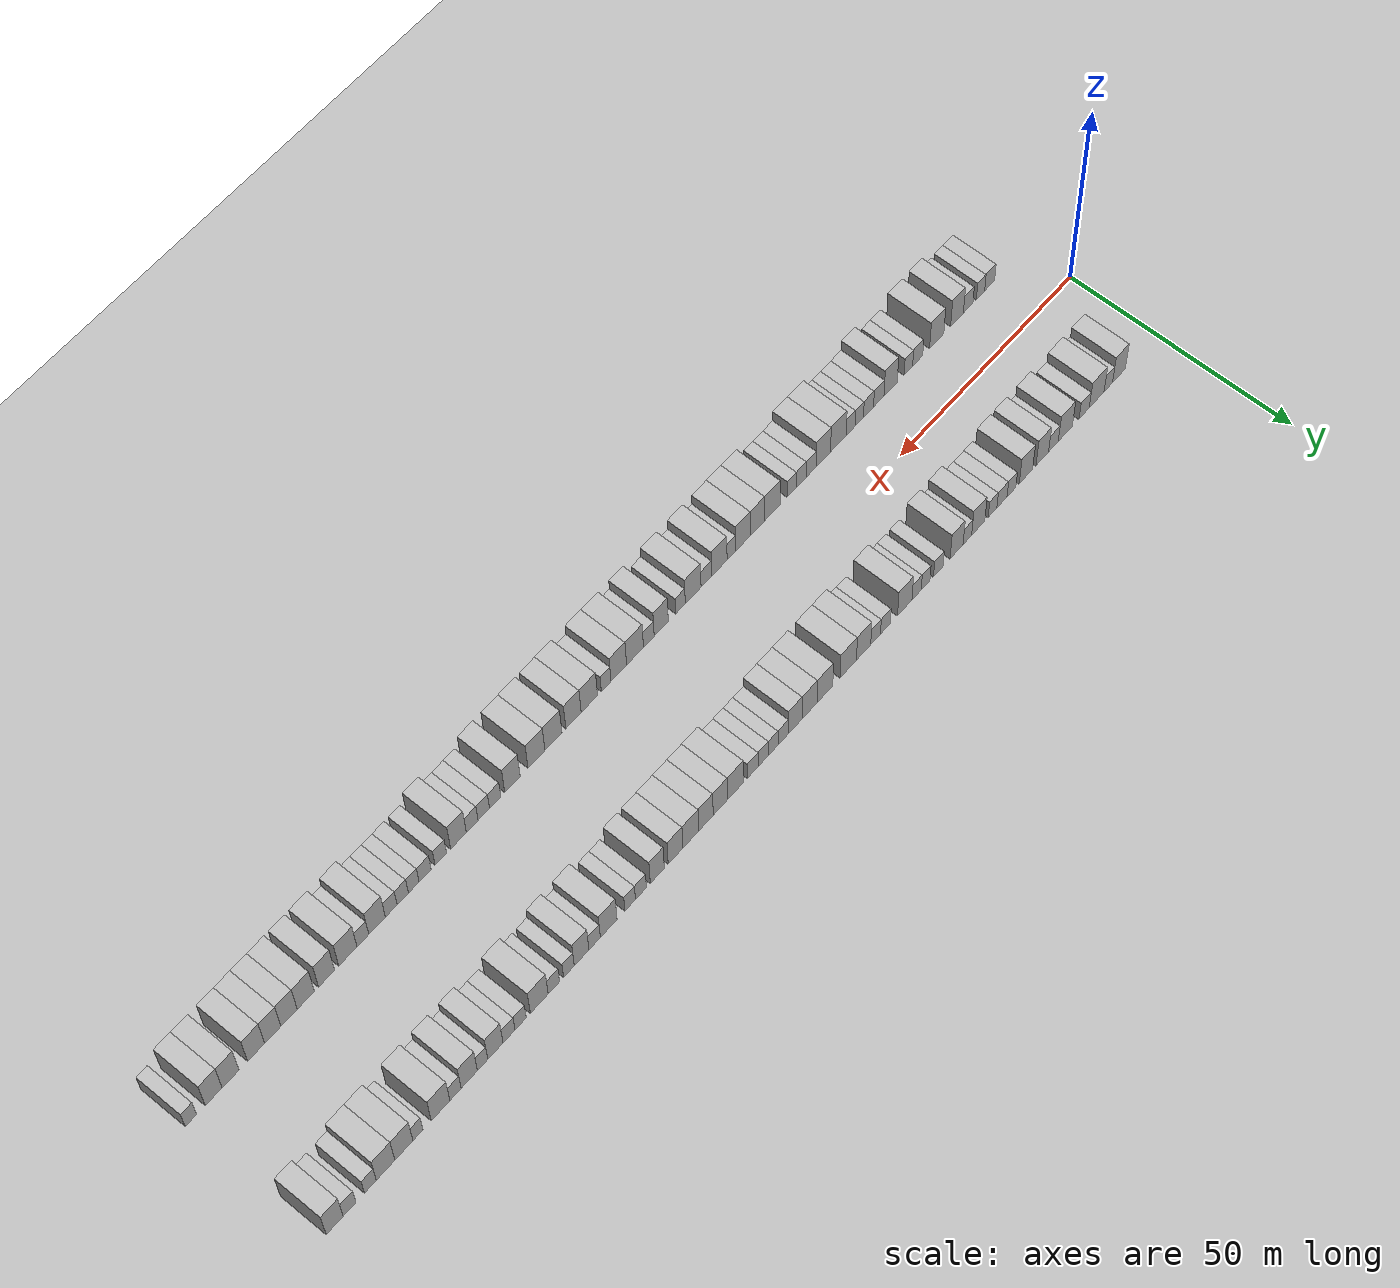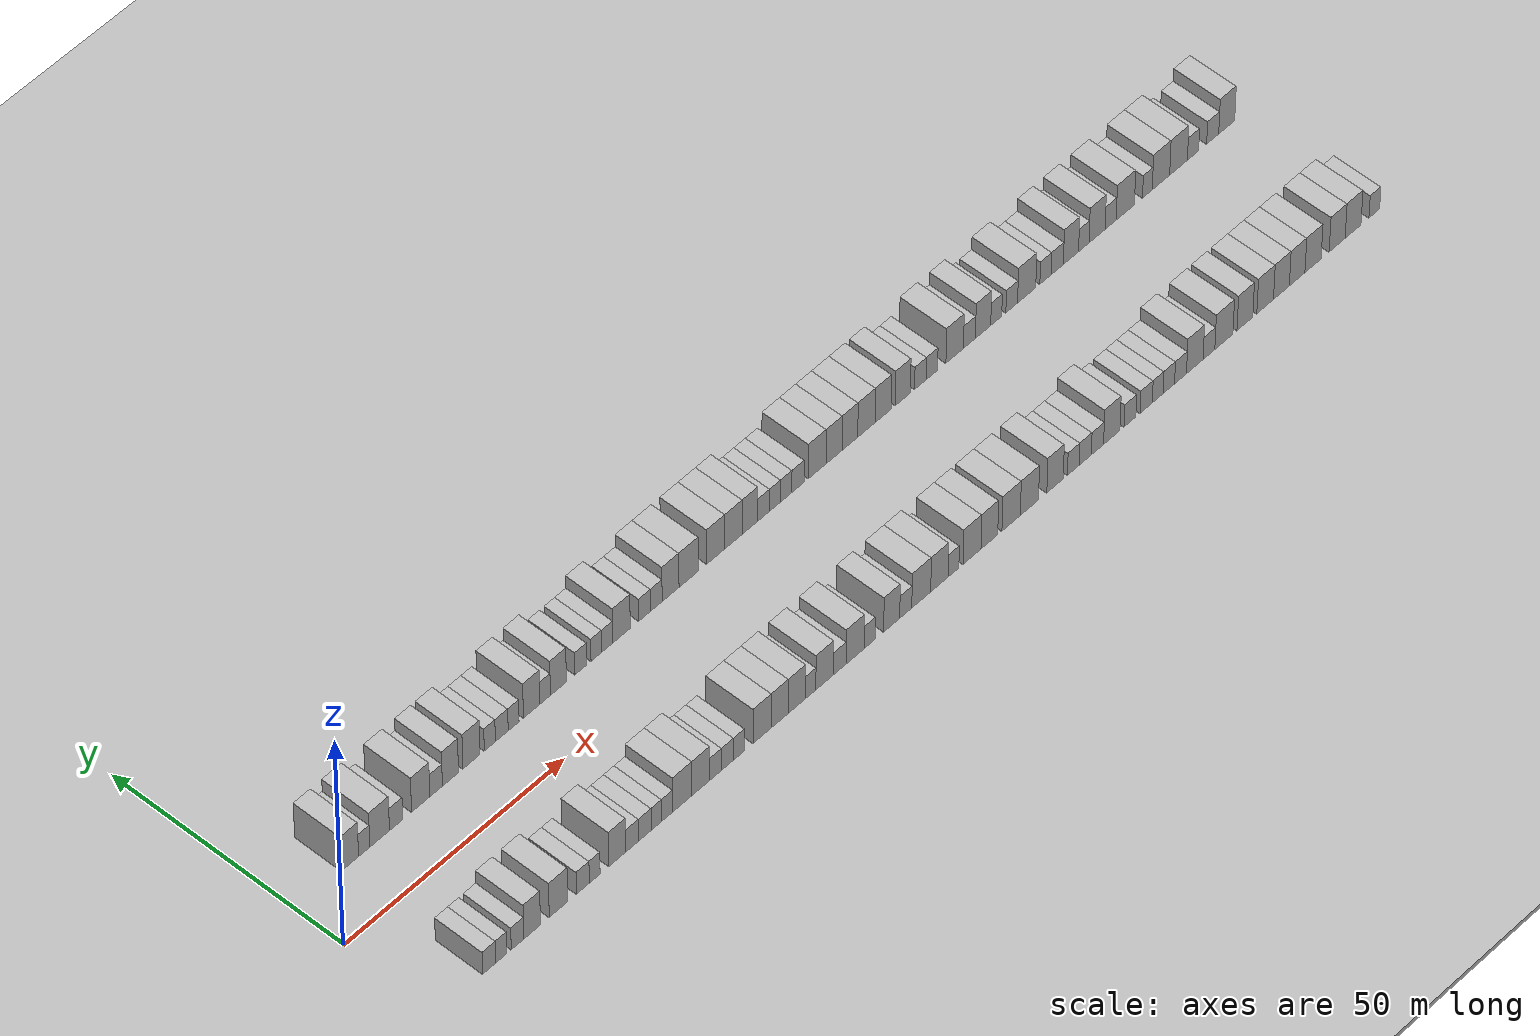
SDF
<?xml version="1.0" encoding="utf-8"?>

<sdf version="1.6">

   <world name="default">

      <gui fullscreen="0">

         <camera name="user_camera">

            <pose>-15 0 4.57585 0 0 0</pose>

            <view_controller>orbit</view_controller>

         </camera>

      </gui>

      <scene>

         <sky>

           <clouds>

             <speed>12</speed>

           </clouds>

         </sky>

         <ambient>0.4 0.4 0.4 1</ambient>

         <background>0.7 0.7 0.7 1</background>

         <shadows>1</shadows>

      </scene>

      <gravity>0 0 -9.8066</gravity>

      <magnetic_field>6e-06 2.3e-05 -4.2e-05</magnetic_field>

      <physics default="0" name="default_physics" type="ode">

         <ode>

            <solver>

               <type>quick</type>

               <iters>10</iters>

               <sor>1.0</sor>

               <use_dynamic_moi_rescaling>0</use_dynamic_moi_rescaling>

            </solver>

            <constraints>

               <cfm>0</cfm>

               <erp>0.2</erp>

               <contact_max_correcting_vel>100</contact_max_correcting_vel>

               <contact_surface_layer>0.001</contact_surface_layer>

            </constraints>

         </ode>

         <max_step_size>0.004</max_step_size>

         <real_time_factor>1</real_time_factor>

         <real_time_update_rate>250</real_time_update_rate>

      </physics>

      <light name="sun" type="directional">

         <cast_shadows>1</cast_shadows>

         <pose>0 0 10 0 0 0</pose>

         <diffuse>0.8 0.8 0.8 1</diffuse>

         <specular>0.2 0.2 0.2 1</specular>

         <attenuation>

            <range>1000</range>

            <constant>0.9</constant>

            <linear>0.01</linear>

            <quadratic>0.001</quadratic>

         </attenuation>

         <direction>-0.5 0.1 -0.9</direction>

      </light>

      <include>

         <name>ground_plane_1</name>

         <uri>model://HANNAS_ground_plane</uri>

         <pose>0 0 0  0 0 0</pose>

      </include>

      <include>

         <name>ground_plane_2</name>

         <uri>model://HANNAS_ground_plane</uri>

         <pose>100 0 0  0 0 0</pose>

      </include>

      <model name="building_1">

         <static>1</static>

         <pose frame="">11.9355 15.0000 0 0.000000 0.000000 1.570796</pose>

         <link name="link">

            <pose frame="">0 0 4.50 0 0 0</pose>

            <collision name="collision">

               <geometry>

                  <box>

                     <size>10.0000 3.8709 9.0000</size>

                  </box>

               </geometry>

               <max_contacts>10</max_contacts>

               <surface>

                  <contact>

                     <ode/>

                  </contact>

                  <bounce/>

                  <friction>

                     <torsional>

                        <ode/>

                     </torsional>

                     <ode/>

                  </friction>

               </surface>

            </collision>

            <visual name="visual">

               <cast_shadows>0</cast_shadows>

               <geometry>

                  <box>

                     <size>10.0000 3.8709 9.0000</size>

                  </box>

               </geometry>

               <material>

                  <script>

                     <uri>model://HANNAS_wall/materials/scripts</uri>

                     <uri>model://HANNAS_wall/materials/textures</uri>

                     <name>vrc/HANNAS_wall</name>

                  </script>

               </material>

            </visual>

            <self_collide>0</self_collide>

            <enable_wind>0</enable_wind>

            <kinematic>0</kinematic>

         </link>

      </model>

      <model name="building_2">

         <static>1</static>

         <pose frame="">15.1357 15.0000 0 0.000000 0.000000 1.570796</pose>

         <link name="link">

            <pose frame="">0 0 3.00 0 0 0</pose>

            <collision name="collision">

               <geometry>

                  <box>

                     <size>10.0000 2.5296 6.0000</size>

                  </box>

               </geometry>

               <max_contacts>10</max_contacts>

               <surface>

                  <contact>

                     <ode/>

                  </contact>

                  <bounce/>

                  <friction>

                     <torsional>

                        <ode/>

                     </torsional>

                     <ode/>

                  </friction>

               </surface>

            </collision>

            <visual name="visual">

               <cast_shadows>0</cast_shadows>

               <geometry>

                  <box>

                     <size>10.0000 2.5296 6.0000</size>

                  </box>

               </geometry>

               <material>

                  <script>

                     <uri>model://HANNAS_wall/materials/scripts</uri>

                     <uri>model://HANNAS_wall/materials/textures</uri>

                     <name>vrc/HANNAS_wall</name>

                  </script>

               </material>

            </visual>

            <self_collide>0</self_collide>

            <enable_wind>0</enable_wind>

            <kinematic>0</kinematic>

         </link>

      </model>

      <model name="building_3">

         <static>1</static>

         <pose frame="">18.6159 15.0000 0 0.000000 0.000000 1.570796</pose>

         <link name="link">

            <pose frame="">0 0 4.50 0 0 0</pose>

            <collision name="collision">

               <geometry>

                  <box>

                     <size>10.0000 4.4307 9.0000</size>

                  </box>

               </geometry>

               <max_contacts>10</max_contacts>

               <surface>

                  <contact>

                     <ode/>

                  </contact>

                  <bounce/>

                  <friction>

                     <torsional>

                        <ode/>

                     </torsional>

                     <ode/>

                  </friction>

               </surface>

            </collision>

            <visual name="visual">

               <cast_shadows>0</cast_shadows>

               <geometry>

                  <box>

                     <size>10.0000 4.4307 9.0000</size>

                  </box>

               </geometry>

               <material>

                  <script>

                     <uri>model://HANNAS_wall/materials/scripts</uri>

                     <uri>model://HANNAS_wall/materials/textures</uri>

                     <name>vrc/HANNAS_wall</name>

                  </script>

               </material>

            </visual>

            <self_collide>0</self_collide>

            <enable_wind>0</enable_wind>

            <kinematic>0</kinematic>

         </link>

      </model>

      <model name="building_4">

         <static>1</static>

         <pose frame="">22.3298 15.0000 0 0.000000 0.000000 1.570796</pose>

         <link name="link">

            <pose frame="">0 0 3.00 0 0 0</pose>

            <collision name="collision">

               <geometry>

                  <box>

                     <size>10.0000 2.9972 6.0000</size>

                  </box>

               </geometry>

               <max_contacts>10</max_contacts>

               <surface>

                  <contact>

                     <ode/>

                  </contact>

                  <bounce/>

                  <friction>

                     <torsional>

                        <ode/>

                     </torsional>

                     <ode/>

                  </friction>

               </surface>

            </collision>

            <visual name="visual">

               <cast_shadows>0</cast_shadows>

               <geometry>

                  <box>

                     <size>10.0000 2.9972 6.0000</size>

                  </box>

               </geometry>

               <material>

                  <script>

                     <uri>model://HANNAS_wall/materials/scripts</uri>

                     <uri>model://HANNAS_wall/materials/textures</uri>

                     <name>vrc/HANNAS_wall</name>

                  </script>

               </material>

            </visual>

            <self_collide>0</self_collide>

            <enable_wind>0</enable_wind>

            <kinematic>0</kinematic>

         </link>

      </model>

      <model name="building_5">

         <static>1</static>

         <pose frame="">27.8996 15.0000 0 0.000000 0.000000 1.570796</pose>

         <link name="link">

            <pose frame="">0 0 4.50 0 0 0</pose>

            <collision name="collision">

               <geometry>

                  <box>

                     <size>10.0000 4.1425 9.0000</size>

                  </box>

               </geometry>

               <max_contacts>10</max_contacts>

               <surface>

                  <contact>

                     <ode/>

                  </contact>

                  <bounce/>

                  <friction>

                     <torsional>

                        <ode/>

                     </torsional>

                     <ode/>

                  </friction>

               </surface>

            </collision>

            <visual name="visual">

               <cast_shadows>0</cast_shadows>

               <geometry>

                  <box>

                     <size>10.0000 4.1425 9.0000</size>

                  </box>

               </geometry>

               <material>

                  <script>

                     <uri>model://HANNAS_wall/materials/scripts</uri>

                     <uri>model://HANNAS_wall/materials/textures</uri>

                     <name>vrc/HANNAS_wall</name>

                  </script>

               </material>

            </visual>

            <self_collide>0</self_collide>

            <enable_wind>0</enable_wind>

            <kinematic>0</kinematic>

         </link>

      </model>

      <model name="building_6">

         <static>1</static>

         <pose frame="">31.3976 15.0000 0 0.000000 0.000000 1.570796</pose>

         <link name="link">

            <pose frame="">0 0 3.00 0 0 0</pose>

            <collision name="collision">

               <geometry>

                  <box>

                     <size>10.0000 2.8534 6.0000</size>

                  </box>

               </geometry>

               <max_contacts>10</max_contacts>

               <surface>

                  <contact>

                     <ode/>

                  </contact>

                  <bounce/>

                  <friction>

                     <torsional>

                        <ode/>

                     </torsional>

                     <ode/>

                  </friction>

               </surface>

            </collision>

            <visual name="visual">

               <cast_shadows>0</cast_shadows>

               <geometry>

                  <box>

                     <size>10.0000 2.8534 6.0000</size>

                  </box>

               </geometry>

               <material>

                  <script>

                     <uri>model://HANNAS_wall/materials/scripts</uri>

                     <uri>model://HANNAS_wall/materials/textures</uri>

                     <name>vrc/HANNAS_wall</name>

                  </script>

               </material>

            </visual>

            <self_collide>0</self_collide>

            <enable_wind>0</enable_wind>

            <kinematic>0</kinematic>

         </link>

      </model>

      <model name="building_7">

         <static>1</static>

         <pose frame="">34.6530 15.0000 0 0.000000 0.000000 1.570796</pose>

         <link name="link">

            <pose frame="">0 0 4.50 0 0 0</pose>

            <collision name="collision">

               <geometry>

                  <box>

                     <size>10.0000 3.6575 9.0000</size>

                  </box>

               </geometry>

               <max_contacts>10</max_contacts>

               <surface>

                  <contact>

                     <ode/>

                  </contact>

                  <bounce/>

                  <friction>

                     <torsional>

                        <ode/>

                     </torsional>

                     <ode/>

                  </friction>

               </surface>

            </collision>

            <visual name="visual">

               <cast_shadows>0</cast_shadows>

               <geometry>

                  <box>

                     <size>10.0000 3.6575 9.0000</size>

                  </box>

               </geometry>

               <material>

                  <script>

                     <uri>model://HANNAS_wall/materials/scripts</uri>

                     <uri>model://HANNAS_wall/materials/textures</uri>

                     <name>vrc/HANNAS_wall</name>

                  </script>

               </material>

            </visual>

            <self_collide>0</self_collide>

            <enable_wind>0</enable_wind>

            <kinematic>0</kinematic>

         </link>

      </model>

      <model name="building_8">

         <static>1</static>

         <pose frame="">39.4240 15.0000 0 0.000000 0.000000 1.570796</pose>

         <link name="link">

            <pose frame="">0 0 4.50 0 0 0</pose>

            <collision name="collision">

               <geometry>

                  <box>

                     <size>10.0000 3.8845 9.0000</size>

                  </box>

               </geometry>

               <max_contacts>10</max_contacts>

               <surface>

                  <contact>

                     <ode/>

                  </contact>

                  <bounce/>

                  <friction>

                     <torsional>

                        <ode/>

                     </torsional>

                     <ode/>

                  </friction>

               </surface>

            </collision>

            <visual name="visual">

               <cast_shadows>0</cast_shadows>

               <geometry>

                  <box>

                     <size>10.0000 3.8845 9.0000</size>

                  </box>

               </geometry>

               <material>

                  <script>

                     <uri>model://HANNAS_wall/materials/scripts</uri>

                     <uri>model://HANNAS_wall/materials/textures</uri>

                     <name>vrc/HANNAS_wall</name>

                  </script>

               </material>

            </visual>

            <self_collide>0</self_collide>

            <enable_wind>0</enable_wind>

            <kinematic>0</kinematic>

         </link>

      </model>

      <model name="building_9">

         <static>1</static>

         <pose frame="">43.6304 15.0000 0 0.000000 0.000000 1.570796</pose>

         <link name="link">

            <pose frame="">0 0 3.00 0 0 0</pose>

            <collision name="collision">

               <geometry>

                  <box>

                     <size>10.0000 2.5283 6.0000</size>

                  </box>

               </geometry>

               <max_contacts>10</max_contacts>

               <surface>

                  <contact>

                     <ode/>

                  </contact>

                  <bounce/>

                  <friction>

                     <torsional>

                        <ode/>

                     </torsional>

                     <ode/>

                  </friction>

               </surface>

            </collision>

            <visual name="visual">

               <cast_shadows>0</cast_shadows>

               <geometry>

                  <box>

                     <size>10.0000 2.5283 6.0000</size>

                  </box>

               </geometry>

               <material>

                  <script>

                     <uri>model://HANNAS_wall/materials/scripts</uri>

                     <uri>model://HANNAS_wall/materials/textures</uri>

                     <name>vrc/HANNAS_wall</name>

                  </script>

               </material>

            </visual>

            <self_collide>0</self_collide>

            <enable_wind>0</enable_wind>

            <kinematic>0</kinematic>

         </link>

      </model>

      <model name="building_10">

         <static>1</static>

         <pose frame="">46.3620 15.0000 0 0.000000 0.000000 1.570796</pose>

         <link name="link">

            <pose frame="">0 0 3.00 0 0 0</pose>

            <collision name="collision">

               <geometry>

                  <box>

                     <size>10.0000 2.9349 6.0000</size>

                  </box>

               </geometry>

               <max_contacts>10</max_contacts>

               <surface>

                  <contact>

                     <ode/>

                  </contact>

                  <bounce/>

                  <friction>

                     <torsional>

                        <ode/>

                     </torsional>

                     <ode/>

                  </friction>

               </surface>

            </collision>

            <visual name="visual">

               <cast_shadows>0</cast_shadows>

               <geometry>

                  <box>

                     <size>10.0000 2.9349 6.0000</size>

                  </box>

               </geometry>

               <material>

                  <script>

                     <uri>model://HANNAS_wall/materials/scripts</uri>

                     <uri>model://HANNAS_wall/materials/textures</uri>

                     <name>vrc/HANNAS_wall</name>

                  </script>

               </material>

            </visual>

            <self_collide>0</self_collide>

            <enable_wind>0</enable_wind>

            <kinematic>0</kinematic>

         </link>

      </model>

      <model name="building_11">

         <static>1</static>

         <pose frame="">49.0717 15.0000 0 0.000000 0.000000 1.570796</pose>

         <link name="link">

            <pose frame="">0 0 3.00 0 0 0</pose>

            <collision name="collision">

               <geometry>

                  <box>

                     <size>10.0000 2.4846 6.0000</size>

                  </box>

               </geometry>

               <max_contacts>10</max_contacts>

               <surface>

                  <contact>

                     <ode/>

                  </contact>

                  <bounce/>

                  <friction>

                     <torsional>

                        <ode/>

                     </torsional>

                     <ode/>

                  </friction>

               </surface>

            </collision>

            <visual name="visual">

               <cast_shadows>0</cast_shadows>

               <geometry>

                  <box>

                     <size>10.0000 2.4846 6.0000</size>

                  </box>

               </geometry>

               <material>

                  <script>

                     <uri>model://HANNAS_wall/materials/scripts</uri>

                     <uri>model://HANNAS_wall/materials/textures</uri>

                     <name>vrc/HANNAS_wall</name>

                  </script>

               </material>

            </visual>

            <self_collide>0</self_collide>

            <enable_wind>0</enable_wind>

            <kinematic>0</kinematic>

         </link>

      </model>

      <model name="building_12">

         <static>1</static>

         <pose frame="">53.1930 15.0000 0 0.000000 0.000000 1.570796</pose>

         <link name="link">

            <pose frame="">0 0 4.50 0 0 0</pose>

            <collision name="collision">

               <geometry>

                  <box>

                     <size>10.0000 3.7579 9.0000</size>

                  </box>

               </geometry>

               <max_contacts>10</max_contacts>

               <surface>

                  <contact>

                     <ode/>

                  </contact>

                  <bounce/>

                  <friction>

                     <torsional>

                        <ode/>

                     </torsional>

                     <ode/>

                  </friction>

               </surface>

            </collision>

            <visual name="visual">

               <cast_shadows>0</cast_shadows>

               <geometry>

                  <box>

                     <size>10.0000 3.7579 9.0000</size>

                  </box>

               </geometry>

               <material>

                  <script>

                     <uri>model://HANNAS_wall/materials/scripts</uri>

                     <uri>model://HANNAS_wall/materials/textures</uri>

                     <name>vrc/HANNAS_wall</name>

                  </script>

               </material>

            </visual>

            <self_collide>0</self_collide>

            <enable_wind>0</enable_wind>

            <kinematic>0</kinematic>

         </link>

      </model>

      <model name="building_13">

         <static>1</static>

         <pose frame="">56.2924 15.0000 0 0.000000 0.000000 1.570796</pose>

         <link name="link">

            <pose frame="">0 0 3.00 0 0 0</pose>

            <collision name="collision">

               <geometry>

                  <box>

                     <size>10.0000 2.4409 6.0000</size>

                  </box>

               </geometry>

               <max_contacts>10</max_contacts>

               <surface>

                  <contact>

                     <ode/>

                  </contact>

                  <bounce/>

                  <friction>

                     <torsional>

                        <ode/>

                     </torsional>

                     <ode/>

                  </friction>

               </surface>

            </collision>

            <visual name="visual">

               <cast_shadows>0</cast_shadows>

               <geometry>

                  <box>

                     <size>10.0000 2.4409 6.0000</size>

                  </box>

               </geometry>

               <material>

                  <script>

                     <uri>model://HANNAS_wall/materials/scripts</uri>

                     <uri>model://HANNAS_wall/materials/textures</uri>

                     <name>vrc/HANNAS_wall</name>

                  </script>

               </material>

            </visual>

            <self_collide>0</self_collide>

            <enable_wind>0</enable_wind>

            <kinematic>0</kinematic>

         </link>

      </model>

      <model name="building_14">

         <static>1</static>

         <pose frame="">59.3512 15.0000 0 0.000000 0.000000 1.570796</pose>

         <link name="link">

            <pose frame="">0 0 4.50 0 0 0</pose>

            <collision name="collision">

               <geometry>

                  <box>

                     <size>10.0000 3.6767 9.0000</size>

                  </box>

               </geometry>

               <max_contacts>10</max_contacts>

               <surface>

                  <contact>

                     <ode/>

                  </contact>

                  <bounce/>

                  <friction>

                     <torsional>

                        <ode/>

                     </torsional>

                     <ode/>

                  </friction>

               </surface>

            </collision>

            <visual name="visual">

               <cast_shadows>0</cast_shadows>

               <geometry>

                  <box>

                     <size>10.0000 3.6767 9.0000</size>

                  </box>

               </geometry>

               <material>

                  <script>

                     <uri>model://HANNAS_wall/materials/scripts</uri>

                     <uri>model://HANNAS_wall/materials/textures</uri>

                     <name>vrc/HANNAS_wall</name>

                  </script>

               </material>

            </visual>

            <self_collide>0</self_collide>

            <enable_wind>0</enable_wind>

            <kinematic>0</kinematic>

         </link>

      </model>

      <model name="building_15">

         <static>1</static>

         <pose frame="">64.5397 15.0000 0 0.000000 0.000000 1.570796</pose>

         <link name="link">

            <pose frame="">0 0 3.00 0 0 0</pose>

            <collision name="collision">

               <geometry>

                  <box>

                     <size>10.0000 2.7004 6.0000</size>

                  </box>

               </geometry>

               <max_contacts>10</max_contacts>

               <surface>

                  <contact>

                     <ode/>

                  </contact>

                  <bounce/>

                  <friction>

                     <torsional>

                        <ode/>

                     </torsional>

                     <ode/>

                  </friction>

               </surface>

            </collision>

            <visual name="visual">

               <cast_shadows>0</cast_shadows>

               <geometry>

                  <box>

                     <size>10.0000 2.7004 6.0000</size>

                  </box>

               </geometry>

               <material>

                  <script>

                     <uri>model://HANNAS_wall/materials/scripts</uri>

                     <uri>model://HANNAS_wall/materials/textures</uri>

                     <name>vrc/HANNAS_wall</name>

                  </script>

               </material>

            </visual>

            <self_collide>0</self_collide>

            <enable_wind>0</enable_wind>

            <kinematic>0</kinematic>

         </link>

      </model>

      <model name="building_16">

         <static>1</static>

         <pose frame="">68.1228 15.0000 0 0.000000 0.000000 1.570796</pose>

         <link name="link">

            <pose frame="">0 0 3.00 0 0 0</pose>

            <collision name="collision">

               <geometry>

                  <box>

                     <size>10.0000 2.4657 6.0000</size>

                  </box>

               </geometry>

               <max_contacts>10</max_contacts>

               <surface>

                  <contact>

                     <ode/>

                  </contact>

                  <bounce/>

                  <friction>

                     <torsional>

                        <ode/>

                     </torsional>

                     <ode/>

                  </friction>

               </surface>

            </collision>

            <visual name="visual">

               <cast_shadows>0</cast_shadows>

               <geometry>

                  <box>

                     <size>10.0000 2.4657 6.0000</size>

                  </box>

               </geometry>

               <material>

                  <script>

                     <uri>model://HANNAS_wall/materials/scripts</uri>

                     <uri>model://HANNAS_wall/materials/textures</uri>

                     <name>vrc/HANNAS_wall</name>

                  </script>

               </material>

            </visual>

            <self_collide>0</self_collide>

            <enable_wind>0</enable_wind>

            <kinematic>0</kinematic>

         </link>

      </model>

      <model name="building_17">

         <static>1</static>

         <pose frame="">70.6452 15.0000 0 0.000000 0.000000 1.570796</pose>

         <link name="link">

            <pose frame="">0 0 3.00 0 0 0</pose>

            <collision name="collision">

               <geometry>

                  <box>

                     <size>10.0000 2.5791 6.0000</size>

                  </box>

               </geometry>

               <max_contacts>10</max_contacts>

               <surface>

                  <contact>

                     <ode/>

                  </contact>

                  <bounce/>

                  <friction>

                     <torsional>

                        <ode/>

                     </torsional>

                     <ode/>

                  </friction>

               </surface>

            </collision>

            <visual name="visual">

               <cast_shadows>0</cast_shadows>

               <geometry>

                  <box>

                     <size>10.0000 2.5791 6.0000</size>

                  </box>

               </geometry>

               <material>

                  <script>

                     <uri>model://HANNAS_wall/materials/scripts</uri>

                     <uri>model://HANNAS_wall/materials/textures</uri>

                     <name>vrc/HANNAS_wall</name>

                  </script>

               </material>

            </visual>

            <self_collide>0</self_collide>

            <enable_wind>0</enable_wind>

            <kinematic>0</kinematic>

         </link>

      </model>

      <model name="building_18">

         <static>1</static>

         <pose frame="">73.9491 15.0000 0 0.000000 0.000000 1.570796</pose>

         <link name="link">

            <pose frame="">0 0 4.50 0 0 0</pose>

            <collision name="collision">

               <geometry>

                  <box>

                     <size>10.0000 4.0286 9.0000</size>

                  </box>

               </geometry>

               <max_contacts>10</max_contacts>

               <surface>

                  <contact>

                     <ode/>

                  </contact>

                  <bounce/>

                  <friction>

                     <torsional>

                        <ode/>

                     </torsional>

                     <ode/>

                  </friction>

               </surface>

            </collision>

            <visual name="visual">

               <cast_shadows>0</cast_shadows>

               <geometry>

                  <box>

                     <size>10.0000 4.0286 9.0000</size>

                  </box>

               </geometry>

               <material>

                  <script>

                     <uri>model://HANNAS_wall/materials/scripts</uri>

                     <uri>model://HANNAS_wall/materials/textures</uri>

                     <name>vrc/HANNAS_wall</name>

                  </script>

               </material>

            </visual>

            <self_collide>0</self_collide>

            <enable_wind>0</enable_wind>

            <kinematic>0</kinematic>

         </link>

      </model>

      <model name="building_19">

         <static>1</static>

         <pose frame="">79.3284 15.0000 0 0.000000 0.000000 1.570796</pose>

         <link name="link">

            <pose frame="">0 0 3.00 0 0 0</pose>

            <collision name="collision">

               <geometry>

                  <box>

                     <size>10.0000 2.7300 6.0000</size>

                  </box>

               </geometry>

               <max_contacts>10</max_contacts>

               <surface>

                  <contact>

                     <ode/>

                  </contact>

                  <bounce/>

                  <friction>

                     <torsional>

                        <ode/>

                     </torsional>

                     <ode/>

                  </friction>

               </surface>

            </collision>

            <visual name="visual">

               <cast_shadows>0</cast_shadows>

               <geometry>

                  <box>

                     <size>10.0000 2.7300 6.0000</size>

                  </box>

               </geometry>

               <material>

                  <script>

                     <uri>model://HANNAS_wall/materials/scripts</uri>

                     <uri>model://HANNAS_wall/materials/textures</uri>

                     <name>vrc/HANNAS_wall</name>

                  </script>

               </material>

            </visual>

            <self_collide>0</self_collide>

            <enable_wind>0</enable_wind>

            <kinematic>0</kinematic>

         </link>

      </model>

      <model name="building_20">

         <static>1</static>

         <pose frame="">82.0445 15.0000 0 0.000000 0.000000 1.570796</pose>

         <link name="link">

            <pose frame="">0 0 3.00 0 0 0</pose>

            <collision name="collision">

               <geometry>

                  <box>

                     <size>10.0000 2.7021 6.0000</size>

                  </box>

               </geometry>

               <max_contacts>10</max_contacts>

               <surface>

                  <contact>

                     <ode/>

                  </contact>

                  <bounce/>

                  <friction>

                     <torsional>

                        <ode/>

                     </torsional>

                     <ode/>

                  </friction>

               </surface>

            </collision>

            <visual name="visual">

               <cast_shadows>0</cast_shadows>

               <geometry>

                  <box>

                     <size>10.0000 2.7021 6.0000</size>

                  </box>

               </geometry>

               <material>

                  <script>

                     <uri>model://HANNAS_wall/materials/scripts</uri>

                     <uri>model://HANNAS_wall/materials/textures</uri>

                     <name>vrc/HANNAS_wall</name>

                  </script>

               </material>

            </visual>

            <self_collide>0</self_collide>

            <enable_wind>0</enable_wind>

            <kinematic>0</kinematic>

         </link>

      </model>

      <model name="building_21">

         <static>1</static>

         <pose frame="">85.3691 15.0000 0 0.000000 0.000000 1.570796</pose>

         <link name="link">

            <pose frame="">0 0 4.50 0 0 0</pose>

            <collision name="collision">

               <geometry>

                  <box>

                     <size>10.0000 3.9471 9.0000</size>

                  </box>

               </geometry>

               <max_contacts>10</max_contacts>

               <surface>

                  <contact>

                     <ode/>

                  </contact>

                  <bounce/>

                  <friction>

                     <torsional>

                        <ode/>

                     </torsional>

                     <ode/>

                  </friction>

               </surface>

            </collision>

            <visual name="visual">

               <cast_shadows>0</cast_shadows>

               <geometry>

                  <box>

                     <size>10.0000 3.9471 9.0000</size>

                  </box>

               </geometry>

               <material>

                  <script>

                     <uri>model://HANNAS_wall/materials/scripts</uri>

                     <uri>model://HANNAS_wall/materials/textures</uri>

                     <name>vrc/HANNAS_wall</name>

                  </script>

               </material>

            </visual>

            <self_collide>0</self_collide>

            <enable_wind>0</enable_wind>

            <kinematic>0</kinematic>

         </link>

      </model>

      <model name="building_22">

         <static>1</static>

         <pose frame="">89.5817 15.0000 0 0.000000 0.000000 1.570796</pose>

         <link name="link">

            <pose frame="">0 0 4.50 0 0 0</pose>

            <collision name="collision">

               <geometry>

                  <box>

                     <size>10.0000 4.4781 9.0000</size>

                  </box>

               </geometry>

               <max_contacts>10</max_contacts>

               <surface>

                  <contact>

                     <ode/>

                  </contact>

                  <bounce/>

                  <friction>

                     <torsional>

                        <ode/>

                     </torsional>

                     <ode/>

                  </friction>

               </surface>

            </collision>

            <visual name="visual">

               <cast_shadows>0</cast_shadows>

               <geometry>

                  <box>

                     <size>10.0000 4.4781 9.0000</size>

                  </box>

               </geometry>

               <material>

                  <script>

                     <uri>model://HANNAS_wall/materials/scripts</uri>

                     <uri>model://HANNAS_wall/materials/textures</uri>

                     <name>vrc/HANNAS_wall</name>

                  </script>

               </material>

            </visual>

            <self_collide>0</self_collide>

            <enable_wind>0</enable_wind>

            <kinematic>0</kinematic>

         </link>

      </model>

      <model name="building_23">

         <static>1</static>

         <pose frame="">95.9513 15.0000 0 0.000000 0.000000 1.570796</pose>

         <link name="link">

            <pose frame="">0 0 4.50 0 0 0</pose>

            <collision name="collision">

               <geometry>

                  <box>

                     <size>10.0000 4.2611 9.0000</size>

                  </box>

               </geometry>

               <max_contacts>10</max_contacts>

               <surface>

                  <contact>

                     <ode/>

                  </contact>

                  <bounce/>

                  <friction>

                     <torsional>

                        <ode/>

                     </torsional>

                     <ode/>

                  </friction>

               </surface>

            </collision>

            <visual name="visual">

               <cast_shadows>0</cast_shadows>

               <geometry>

                  <box>

                     <size>10.0000 4.2611 9.0000</size>

                  </box>

               </geometry>

               <material>

                  <script>

                     <uri>model://HANNAS_wall/materials/scripts</uri>

                     <uri>model://HANNAS_wall/materials/textures</uri>

                     <name>vrc/HANNAS_wall</name>

                  </script>

               </material>

            </visual>

            <self_collide>0</self_collide>

            <enable_wind>0</enable_wind>

            <kinematic>0</kinematic>

         </link>

      </model>

      <model name="building_24">

         <static>1</static>

         <pose frame="">100.1310 15.0000 0 0.000000 0.000000 1.570796</pose>

         <link name="link">

            <pose frame="">0 0 4.50 0 0 0</pose>

            <collision name="collision">

               <geometry>

                  <box>

                     <size>10.0000 4.0983 9.0000</size>

                  </box>

               </geometry>

               <max_contacts>10</max_contacts>

               <surface>

                  <contact>

                     <ode/>

                  </contact>

                  <bounce/>

                  <friction>

                     <torsional>

                        <ode/>

                     </torsional>

                     <ode/>

                  </friction>

               </surface>

            </collision>

            <visual name="visual">

               <cast_shadows>0</cast_shadows>

               <geometry>

                  <box>

                     <size>10.0000 4.0983 9.0000</size>

                  </box>

               </geometry>

               <material>

                  <script>

                     <uri>model://HANNAS_wall/materials/scripts</uri>

                     <uri>model://HANNAS_wall/materials/textures</uri>

                     <name>vrc/HANNAS_wall</name>

                  </script>

               </material>

            </visual>

            <self_collide>0</self_collide>

            <enable_wind>0</enable_wind>

            <kinematic>0</kinematic>

         </link>

      </model>

      <model name="building_25">

         <static>1</static>

         <pose frame="">104.0064 15.0000 0 0.000000 0.000000 1.570796</pose>

         <link name="link">

            <pose frame="">0 0 4.50 0 0 0</pose>

            <collision name="collision">

               <geometry>

                  <box>

                     <size>10.0000 3.6526 9.0000</size>

                  </box>

               </geometry>

               <max_contacts>10</max_contacts>

               <surface>

                  <contact>

                     <ode/>

                  </contact>

                  <bounce/>

                  <friction>

                     <torsional>

                        <ode/>

                     </torsional>

                     <ode/>

                  </friction>

               </surface>

            </collision>

            <visual name="visual">

               <cast_shadows>0</cast_shadows>

               <geometry>

                  <box>

                     <size>10.0000 3.6526 9.0000</size>

                  </box>

               </geometry>

               <material>

                  <script>

                     <uri>model://HANNAS_wall/materials/scripts</uri>

                     <uri>model://HANNAS_wall/materials/textures</uri>

                     <name>vrc/HANNAS_wall</name>

                  </script>

               </material>

            </visual>

            <self_collide>0</self_collide>

            <enable_wind>0</enable_wind>

            <kinematic>0</kinematic>

         </link>

      </model>

      <model name="building_26">

         <static>1</static>

         <pose frame="">107.2340 15.0000 0 0.000000 0.000000 1.570796</pose>

         <link name="link">

            <pose frame="">0 0 3.00 0 0 0</pose>

            <collision name="collision">

               <geometry>

                  <box>

                     <size>10.0000 2.8026 6.0000</size>

                  </box>

               </geometry>

               <max_contacts>10</max_contacts>

               <surface>

                  <contact>

                     <ode/>

                  </contact>

                  <bounce/>

                  <friction>

                     <torsional>

                        <ode/>

                     </torsional>

                     <ode/>

                  </friction>

               </surface>

            </collision>

            <visual name="visual">

               <cast_shadows>0</cast_shadows>

               <geometry>

                  <box>

                     <size>10.0000 2.8026 6.0000</size>

                  </box>

               </geometry>

               <material>

                  <script>

                     <uri>model://HANNAS_wall/materials/scripts</uri>

                     <uri>model://HANNAS_wall/materials/textures</uri>

                     <name>vrc/HANNAS_wall</name>

                  </script>

               </material>

            </visual>

            <self_collide>0</self_collide>

            <enable_wind>0</enable_wind>

            <kinematic>0</kinematic>

         </link>

      </model>

      <model name="building_27">

         <static>1</static>

         <pose frame="">109.9182 15.0000 0 0.000000 0.000000 1.570796</pose>

         <link name="link">

            <pose frame="">0 0 3.00 0 0 0</pose>

            <collision name="collision">

               <geometry>

                  <box>

                     <size>10.0000 2.5657 6.0000</size>

                  </box>

               </geometry>

               <max_contacts>10</max_contacts>

               <surface>

                  <contact>

                     <ode/>

                  </contact>

                  <bounce/>

                  <friction>

                     <torsional>

                        <ode/>

                     </torsional>

                     <ode/>

                  </friction>

               </surface>

            </collision>

            <visual name="visual">

               <cast_shadows>0</cast_shadows>

               <geometry>

                  <box>

                     <size>10.0000 2.5657 6.0000</size>

                  </box>

               </geometry>

               <material>

                  <script>

                     <uri>model://HANNAS_wall/materials/scripts</uri>

                     <uri>model://HANNAS_wall/materials/textures</uri>

                     <name>vrc/HANNAS_wall</name>

                  </script>

               </material>

            </visual>

            <self_collide>0</self_collide>

            <enable_wind>0</enable_wind>

            <kinematic>0</kinematic>

         </link>

      </model>

      <model name="building_28">

         <static>1</static>

         <pose frame="">112.5462 15.0000 0 0.000000 0.000000 1.570796</pose>

         <link name="link">

            <pose frame="">0 0 3.00 0 0 0</pose>

            <collision name="collision">

               <geometry>

                  <box>

                     <size>10.0000 2.6904 6.0000</size>

                  </box>

               </geometry>

               <max_contacts>10</max_contacts>

               <surface>

                  <contact>

                     <ode/>

                  </contact>

                  <bounce/>

                  <friction>

                     <torsional>

                        <ode/>

                     </torsional>

                     <ode/>

                  </friction>

               </surface>

            </collision>

            <visual name="visual">

               <cast_shadows>0</cast_shadows>

               <geometry>

                  <box>

                     <size>10.0000 2.6904 6.0000</size>

                  </box>

               </geometry>

               <material>

                  <script>

                     <uri>model://HANNAS_wall/materials/scripts</uri>

                     <uri>model://HANNAS_wall/materials/textures</uri>

                     <name>vrc/HANNAS_wall</name>

                  </script>

               </material>

            </visual>

            <self_collide>0</self_collide>

            <enable_wind>0</enable_wind>

            <kinematic>0</kinematic>

         </link>

      </model>

      <model name="building_29">

         <static>1</static>

         <pose frame="">115.3470 15.0000 0 0.000000 0.000000 1.570796</pose>

         <link name="link">

            <pose frame="">0 0 3.00 0 0 0</pose>

            <collision name="collision">

               <geometry>

                  <box>

                     <size>10.0000 2.9112 6.0000</size>

                  </box>

               </geometry>

               <max_contacts>10</max_contacts>

               <surface>

                  <contact>

                     <ode/>

                  </contact>

                  <bounce/>

                  <friction>

                     <torsional>

                        <ode/>

                     </torsional>

                     <ode/>

                  </friction>

               </surface>

            </collision>

            <visual name="visual">

               <cast_shadows>0</cast_shadows>

               <geometry>

                  <box>

                     <size>10.0000 2.9112 6.0000</size>

                  </box>

               </geometry>

               <material>

                  <script>

                     <uri>model://HANNAS_wall/materials/scripts</uri>

                     <uri>model://HANNAS_wall/materials/textures</uri>

                     <name>vrc/HANNAS_wall</name>

                  </script>

               </material>

            </visual>

            <self_collide>0</self_collide>

            <enable_wind>0</enable_wind>

            <kinematic>0</kinematic>

         </link>

      </model>

      <model name="building_30">

         <static>1</static>

         <pose frame="">119.9015 15.0000 0 0.000000 0.000000 1.570796</pose>

         <link name="link">

            <pose frame="">0 0 4.50 0 0 0</pose>

            <collision name="collision">

               <geometry>

                  <box>

                     <size>10.0000 4.1978 9.0000</size>

                  </box>

               </geometry>

               <max_contacts>10</max_contacts>

               <surface>

                  <contact>

                     <ode/>

                  </contact>

                  <bounce/>

                  <friction>

                     <torsional>

                        <ode/>

                     </torsional>

                     <ode/>

                  </friction>

               </surface>

            </collision>

            <visual name="visual">

               <cast_shadows>0</cast_shadows>

               <geometry>

                  <box>

                     <size>10.0000 4.1978 9.0000</size>

                  </box>

               </geometry>

               <material>

                  <script>

                     <uri>model://HANNAS_wall/materials/scripts</uri>

                     <uri>model://HANNAS_wall/materials/textures</uri>

                     <name>vrc/HANNAS_wall</name>

                  </script>

               </material>

            </visual>

            <self_collide>0</self_collide>

            <enable_wind>0</enable_wind>

            <kinematic>0</kinematic>

         </link>

      </model>

      <model name="building_31">

         <static>1</static>

         <pose frame="">123.9093 15.0000 0 0.000000 0.000000 1.570796</pose>

         <link name="link">

            <pose frame="">0 0 4.50 0 0 0</pose>

            <collision name="collision">

               <geometry>

                  <box>

                     <size>10.0000 3.8177 9.0000</size>

                  </box>

               </geometry>

               <max_contacts>10</max_contacts>

               <surface>

                  <contact>

                     <ode/>

                  </contact>

                  <bounce/>

                  <friction>

                     <torsional>

                        <ode/>

                     </torsional>

                     <ode/>

                  </friction>

               </surface>

            </collision>

            <visual name="visual">

               <cast_shadows>0</cast_shadows>

               <geometry>

                  <box>

                     <size>10.0000 3.8177 9.0000</size>

                  </box>

               </geometry>

               <material>

                  <script>

                     <uri>model://HANNAS_wall/materials/scripts</uri>

                     <uri>model://HANNAS_wall/materials/textures</uri>

                     <name>vrc/HANNAS_wall</name>

                  </script>

               </material>

            </visual>

            <self_collide>0</self_collide>

            <enable_wind>0</enable_wind>

            <kinematic>0</kinematic>

         </link>

      </model>

      <model name="building_32">

         <static>1</static>

         <pose frame="">127.6894 15.0000 0 0.000000 0.000000 1.570796</pose>

         <link name="link">

            <pose frame="">0 0 4.50 0 0 0</pose>

            <collision name="collision">

               <geometry>

                  <box>

                     <size>10.0000 3.7425 9.0000</size>

                  </box>

               </geometry>

               <max_contacts>10</max_contacts>

               <surface>

                  <contact>

                     <ode/>

                  </contact>

                  <bounce/>

                  <friction>

                     <torsional>

                        <ode/>

                     </torsional>

                     <ode/>

                  </friction>

               </surface>

            </collision>

            <visual name="visual">

               <cast_shadows>0</cast_shadows>

               <geometry>

                  <box>

                     <size>10.0000 3.7425 9.0000</size>

                  </box>

               </geometry>

               <material>

                  <script>

                     <uri>model://HANNAS_wall/materials/scripts</uri>

                     <uri>model://HANNAS_wall/materials/textures</uri>

                     <name>vrc/HANNAS_wall</name>

                  </script>

               </material>

            </visual>

            <self_collide>0</self_collide>

            <enable_wind>0</enable_wind>

            <kinematic>0</kinematic>

         </link>

      </model>

      <model name="building_33">

         <static>1</static>

         <pose frame="">131.6490 15.0000 0 0.000000 0.000000 1.570796</pose>

         <link name="link">

            <pose frame="">0 0 4.50 0 0 0</pose>

            <collision name="collision">

               <geometry>

                  <box>

                     <size>10.0000 4.1766 9.0000</size>

                  </box>

               </geometry>

               <max_contacts>10</max_contacts>

               <surface>

                  <contact>

                     <ode/>

                  </contact>

                  <bounce/>

                  <friction>

                     <torsional>

                        <ode/>

                     </torsional>

                     <ode/>

                  </friction>

               </surface>

            </collision>

            <visual name="visual">

               <cast_shadows>0</cast_shadows>

               <geometry>

                  <box>

                     <size>10.0000 4.1766 9.0000</size>

                  </box>

               </geometry>

               <material>

                  <script>

                     <uri>model://HANNAS_wall/materials/scripts</uri>

                     <uri>model://HANNAS_wall/materials/textures</uri>

                     <name>vrc/HANNAS_wall</name>

                  </script>

               </material>

            </visual>

            <self_collide>0</self_collide>

            <enable_wind>0</enable_wind>

            <kinematic>0</kinematic>

         </link>

      </model>

      <model name="building_34">

         <static>1</static>

         <pose frame="">135.6532 15.0000 0 0.000000 0.000000 1.570796</pose>

         <link name="link">

            <pose frame="">0 0 4.50 0 0 0</pose>

            <collision name="collision">

               <geometry>

                  <box>

                     <size>10.0000 3.8319 9.0000</size>

                  </box>

               </geometry>

               <max_contacts>10</max_contacts>

               <surface>

                  <contact>

                     <ode/>

                  </contact>

                  <bounce/>

                  <friction>

                     <torsional>

                        <ode/>

                     </torsional>

                     <ode/>

                  </friction>

               </surface>

            </collision>

            <visual name="visual">

               <cast_shadows>0</cast_shadows>

               <geometry>

                  <box>

                     <size>10.0000 3.8319 9.0000</size>

                  </box>

               </geometry>

               <material>

                  <script>

                     <uri>model://HANNAS_wall/materials/scripts</uri>

                     <uri>model://HANNAS_wall/materials/textures</uri>

                     <name>vrc/HANNAS_wall</name>

                  </script>

               </material>

            </visual>

            <self_collide>0</self_collide>

            <enable_wind>0</enable_wind>

            <kinematic>0</kinematic>

         </link>

      </model>

      <model name="building_35">

         <static>1</static>

         <pose frame="">140.3760 15.0000 0 0.000000 0.000000 1.570796</pose>

         <link name="link">

            <pose frame="">0 0 4.50 0 0 0</pose>

            <collision name="collision">

               <geometry>

                  <box>

                     <size>10.0000 3.6137 9.0000</size>

                  </box>

               </geometry>

               <max_contacts>10</max_contacts>

               <surface>

                  <contact>

                     <ode/>

                  </contact>

                  <bounce/>

                  <friction>

                     <torsional>

                        <ode/>

                     </torsional>

                     <ode/>

                  </friction>

               </surface>

            </collision>

            <visual name="visual">

               <cast_shadows>0</cast_shadows>

               <geometry>

                  <box>

                     <size>10.0000 3.6137 9.0000</size>

                  </box>

               </geometry>

               <material>

                  <script>

                     <uri>model://HANNAS_wall/materials/scripts</uri>

                     <uri>model://HANNAS_wall/materials/textures</uri>

                     <name>vrc/HANNAS_wall</name>

                  </script>

               </material>

            </visual>

            <self_collide>0</self_collide>

            <enable_wind>0</enable_wind>

            <kinematic>0</kinematic>

         </link>

      </model>

      <model name="building_36">

         <static>1</static>

         <pose frame="">144.5920 15.0000 0 0.000000 0.000000 1.570796</pose>

         <link name="link">

            <pose frame="">0 0 3.00 0 0 0</pose>

            <collision name="collision">

               <geometry>

                  <box>

                     <size>10.0000 2.8183 6.0000</size>

                  </box>

               </geometry>

               <max_contacts>10</max_contacts>

               <surface>

                  <contact>

                     <ode/>

                  </contact>

                  <bounce/>

                  <friction>

                     <torsional>

                        <ode/>

                     </torsional>

                     <ode/>

                  </friction>

               </surface>

            </collision>

            <visual name="visual">

               <cast_shadows>0</cast_shadows>

               <geometry>

                  <box>

                     <size>10.0000 2.8183 6.0000</size>

                  </box>

               </geometry>

               <material>

                  <script>

                     <uri>model://HANNAS_wall/materials/scripts</uri>

                     <uri>model://HANNAS_wall/materials/textures</uri>

                     <name>vrc/HANNAS_wall</name>

                  </script>

               </material>

            </visual>

            <self_collide>0</self_collide>

            <enable_wind>0</enable_wind>

            <kinematic>0</kinematic>

         </link>

      </model>

      <model name="building_37">

         <static>1</static>

         <pose frame="">147.3561 15.0000 0 0.000000 0.000000 1.570796</pose>

         <link name="link">

            <pose frame="">0 0 3.00 0 0 0</pose>

            <collision name="collision">

               <geometry>

                  <box>

                     <size>10.0000 2.7098 6.0000</size>

                  </box>

               </geometry>

               <max_contacts>10</max_contacts>

               <surface>

                  <contact>

                     <ode/>

                  </contact>

                  <bounce/>

                  <friction>

                     <torsional>

                        <ode/>

                     </torsional>

                     <ode/>

                  </friction>

               </surface>

            </collision>

            <visual name="visual">

               <cast_shadows>0</cast_shadows>

               <geometry>

                  <box>

                     <size>10.0000 2.7098 6.0000</size>

                  </box>

               </geometry>

               <material>

                  <script>

                     <uri>model://HANNAS_wall/materials/scripts</uri>

                     <uri>model://HANNAS_wall/materials/textures</uri>

                     <name>vrc/HANNAS_wall</name>

                  </script>

               </material>

            </visual>

            <self_collide>0</self_collide>

            <enable_wind>0</enable_wind>

            <kinematic>0</kinematic>

         </link>

      </model>

      <model name="building_38">

         <static>1</static>

         <pose frame="">152.8337 15.0000 0 0.000000 0.000000 1.570796</pose>

         <link name="link">

            <pose frame="">0 0 4.50 0 0 0</pose>

            <collision name="collision">

               <geometry>

                  <box>

                     <size>10.0000 4.2455 9.0000</size>

                  </box>

               </geometry>

               <max_contacts>10</max_contacts>

               <surface>

                  <contact>

                     <ode/>

                  </contact>

                  <bounce/>

                  <friction>

                     <torsional>

                        <ode/>

                     </torsional>

                     <ode/>

                  </friction>

               </surface>

            </collision>

            <visual name="visual">

               <cast_shadows>0</cast_shadows>

               <geometry>

                  <box>

                     <size>10.0000 4.2455 9.0000</size>

                  </box>

               </geometry>

               <material>

                  <script>

                     <uri>model://HANNAS_wall/materials/scripts</uri>

                     <uri>model://HANNAS_wall/materials/textures</uri>

                     <name>vrc/HANNAS_wall</name>

                  </script>

               </material>

            </visual>

            <self_collide>0</self_collide>

            <enable_wind>0</enable_wind>

            <kinematic>0</kinematic>

         </link>

      </model>

      <model name="building_39">

         <static>1</static>

         <pose frame="">156.4042 15.0000 0 0.000000 0.000000 1.570796</pose>

         <link name="link">

            <pose frame="">0 0 3.00 0 0 0</pose>

            <collision name="collision">

               <geometry>

                  <box>

                     <size>10.0000 2.8953 6.0000</size>

                  </box>

               </geometry>

               <max_contacts>10</max_contacts>

               <surface>

                  <contact>

                     <ode/>

                  </contact>

                  <bounce/>

                  <friction>

                     <torsional>

                        <ode/>

                     </torsional>

                     <ode/>

                  </friction>

               </surface>

            </collision>

            <visual name="visual">

               <cast_shadows>0</cast_shadows>

               <geometry>

                  <box>

                     <size>10.0000 2.8953 6.0000</size>

                  </box>

               </geometry>

               <material>

                  <script>

                     <uri>model://HANNAS_wall/materials/scripts</uri>

                     <uri>model://HANNAS_wall/materials/textures</uri>

                     <name>vrc/HANNAS_wall</name>

                  </script>

               </material>

            </visual>

            <self_collide>0</self_collide>

            <enable_wind>0</enable_wind>

            <kinematic>0</kinematic>

         </link>

      </model>

      <model name="building_40">

         <static>1</static>

         <pose frame="">159.7042 15.0000 0 0.000000 0.000000 1.570796</pose>

         <link name="link">

            <pose frame="">0 0 4.50 0 0 0</pose>

            <collision name="collision">

               <geometry>

                  <box>

                     <size>10.0000 3.7048 9.0000</size>

                  </box>

               </geometry>

               <max_contacts>10</max_contacts>

               <surface>

                  <contact>

                     <ode/>

                  </contact>

                  <bounce/>

                  <friction>

                     <torsional>

                        <ode/>

                     </torsional>

                     <ode/>

                  </friction>

               </surface>

            </collision>

            <visual name="visual">

               <cast_shadows>0</cast_shadows>

               <geometry>

                  <box>

                     <size>10.0000 3.7048 9.0000</size>

                  </box>

               </geometry>

               <material>

                  <script>

                     <uri>model://HANNAS_wall/materials/scripts</uri>

                     <uri>model://HANNAS_wall/materials/textures</uri>

                     <name>vrc/HANNAS_wall</name>

                  </script>

               </material>

            </visual>

            <self_collide>0</self_collide>

            <enable_wind>0</enable_wind>

            <kinematic>0</kinematic>

         </link>

      </model>

      <model name="building_41">

         <static>1</static>

         <pose frame="">162.8913 15.0000 0 0.000000 0.000000 1.570796</pose>

         <link name="link">

            <pose frame="">0 0 3.00 0 0 0</pose>

            <collision name="collision">

               <geometry>

                  <box>

                     <size>10.0000 2.6694 6.0000</size>

                  </box>

               </geometry>

               <max_contacts>10</max_contacts>

               <surface>

                  <contact>

                     <ode/>

                  </contact>

                  <bounce/>

                  <friction>

                     <torsional>

                        <ode/>

                     </torsional>

                     <ode/>

                  </friction>

               </surface>

            </collision>

            <visual name="visual">

               <cast_shadows>0</cast_shadows>

               <geometry>

                  <box>

                     <size>10.0000 2.6694 6.0000</size>

                  </box>

               </geometry>

               <material>

                  <script>

                     <uri>model://HANNAS_wall/materials/scripts</uri>

                     <uri>model://HANNAS_wall/materials/textures</uri>

                     <name>vrc/HANNAS_wall</name>

                  </script>

               </material>

            </visual>

            <self_collide>0</self_collide>

            <enable_wind>0</enable_wind>

            <kinematic>0</kinematic>

         </link>

      </model>

      <model name="building_42">

         <static>1</static>

         <pose frame="">166.6520 15.0000 0 0.000000 0.000000 1.570796</pose>

         <link name="link">

            <pose frame="">0 0 3.00 0 0 0</pose>

            <collision name="collision">

               <geometry>

                  <box>

                     <size>10.0000 2.8520 6.0000</size>

                  </box>

               </geometry>

               <max_contacts>10</max_contacts>

               <surface>

                  <contact>

                     <ode/>

                  </contact>

                  <bounce/>

                  <friction>

                     <torsional>

                        <ode/>

                     </torsional>

                     <ode/>

                  </friction>

               </surface>

            </collision>

            <visual name="visual">

               <cast_shadows>0</cast_shadows>

               <geometry>

                  <box>

                     <size>10.0000 2.8520 6.0000</size>

                  </box>

               </geometry>

               <material>

                  <script>

                     <uri>model://HANNAS_wall/materials/scripts</uri>

                     <uri>model://HANNAS_wall/materials/textures</uri>

                     <name>vrc/HANNAS_wall</name>

                  </script>

               </material>

            </visual>

            <self_collide>0</self_collide>

            <enable_wind>0</enable_wind>

            <kinematic>0</kinematic>

         </link>

      </model>

      <model name="building_43">

         <static>1</static>

         <pose frame="">170.2901 15.0000 0 0.000000 0.000000 1.570796</pose>

         <link name="link">

            <pose frame="">0 0 4.50 0 0 0</pose>

            <collision name="collision">

               <geometry>

                  <box>

                     <size>10.0000 4.4242 9.0000</size>

                  </box>

               </geometry>

               <max_contacts>10</max_contacts>

               <surface>

                  <contact>

                     <ode/>

                  </contact>

                  <bounce/>

                  <friction>

                     <torsional>

                        <ode/>

                     </torsional>

                     <ode/>

                  </friction>

               </surface>

            </collision>

            <visual name="visual">

               <cast_shadows>0</cast_shadows>

               <geometry>

                  <box>

                     <size>10.0000 4.4242 9.0000</size>

                  </box>

               </geometry>

               <material>

                  <script>

                     <uri>model://HANNAS_wall/materials/scripts</uri>

                     <uri>model://HANNAS_wall/materials/textures</uri>

                     <name>vrc/HANNAS_wall</name>

                  </script>

               </material>

            </visual>

            <self_collide>0</self_collide>

            <enable_wind>0</enable_wind>

            <kinematic>0</kinematic>

         </link>

      </model>

      <model name="building_44">

         <static>1</static>

         <pose frame="">174.8964 15.0000 0 0.000000 0.000000 1.570796</pose>

         <link name="link">

            <pose frame="">0 0 3.00 0 0 0</pose>

            <collision name="collision">

               <geometry>

                  <box>

                     <size>10.0000 2.7885 6.0000</size>

                  </box>

               </geometry>

               <max_contacts>10</max_contacts>

               <surface>

                  <contact>

                     <ode/>

                  </contact>

                  <bounce/>

                  <friction>

                     <torsional>

                        <ode/>

                     </torsional>

                     <ode/>

                  </friction>

               </surface>

            </collision>

            <visual name="visual">

               <cast_shadows>0</cast_shadows>

               <geometry>

                  <box>

                     <size>10.0000 2.7885 6.0000</size>

                  </box>

               </geometry>

               <material>

                  <script>

                     <uri>model://HANNAS_wall/materials/scripts</uri>

                     <uri>model://HANNAS_wall/materials/textures</uri>

                     <name>vrc/HANNAS_wall</name>

                  </script>

               </material>

            </visual>

            <self_collide>0</self_collide>

            <enable_wind>0</enable_wind>

            <kinematic>0</kinematic>

         </link>

      </model>

      <model name="building_45">

         <static>1</static>

         <pose frame="">177.7703 15.0000 0 0.000000 0.000000 1.570796</pose>

         <link name="link">

            <pose frame="">0 0 3.00 0 0 0</pose>

            <collision name="collision">

               <geometry>

                  <box>

                     <size>10.0000 2.9592 6.0000</size>

                  </box>

               </geometry>

               <max_contacts>10</max_contacts>

               <surface>

                  <contact>

                     <ode/>

                  </contact>

                  <bounce/>

                  <friction>

                     <torsional>

                        <ode/>

                     </torsional>

                     <ode/>

                  </friction>

               </surface>

            </collision>

            <visual name="visual">

               <cast_shadows>0</cast_shadows>

               <geometry>

                  <box>

                     <size>10.0000 2.9592 6.0000</size>

                  </box>

               </geometry>

               <material>

                  <script>

                     <uri>model://HANNAS_wall/materials/scripts</uri>

                     <uri>model://HANNAS_wall/materials/textures</uri>

                     <name>vrc/HANNAS_wall</name>

                  </script>

               </material>

            </visual>

            <self_collide>0</self_collide>

            <enable_wind>0</enable_wind>

            <kinematic>0</kinematic>

         </link>

      </model>

      <model name="building_46">

         <static>1</static>

         <pose frame="">181.1116 15.0000 0 0.000000 0.000000 1.570796</pose>

         <link name="link">

            <pose frame="">0 0 4.50 0 0 0</pose>

            <collision name="collision">

               <geometry>

                  <box>

                     <size>10.0000 3.7234 9.0000</size>

                  </box>

               </geometry>

               <max_contacts>10</max_contacts>

               <surface>

                  <contact>

                     <ode/>

                  </contact>

                  <bounce/>

                  <friction>

                     <torsional>

                        <ode/>

                     </torsional>

                     <ode/>

                  </friction>

               </surface>

            </collision>

            <visual name="visual">

               <cast_shadows>0</cast_shadows>

               <geometry>

                  <box>

                     <size>10.0000 3.7234 9.0000</size>

                  </box>

               </geometry>

               <material>

                  <script>

                     <uri>model://HANNAS_wall/materials/scripts</uri>

                     <uri>model://HANNAS_wall/materials/textures</uri>

                     <name>vrc/HANNAS_wall</name>

                  </script>

               </material>

            </visual>

            <self_collide>0</self_collide>

            <enable_wind>0</enable_wind>

            <kinematic>0</kinematic>

         </link>

      </model>

      <model name="building_47">

         <static>1</static>

         <pose frame="">184.2537 15.0000 0 0.000000 0.000000 1.570796</pose>

         <link name="link">

            <pose frame="">0 0 3.00 0 0 0</pose>

            <collision name="collision">

               <geometry>

                  <box>

                     <size>10.0000 2.5609 6.0000</size>

                  </box>

               </geometry>

               <max_contacts>10</max_contacts>

               <surface>

                  <contact>

                     <ode/>

                  </contact>

                  <bounce/>

                  <friction>

                     <torsional>

                        <ode/>

                     </torsional>

                     <ode/>

                  </friction>

               </surface>

            </collision>

            <visual name="visual">

               <cast_shadows>0</cast_shadows>

               <geometry>

                  <box>

                     <size>10.0000 2.5609 6.0000</size>

                  </box>

               </geometry>

               <material>

                  <script>

                     <uri>model://HANNAS_wall/materials/scripts</uri>

                     <uri>model://HANNAS_wall/materials/textures</uri>

                     <name>vrc/HANNAS_wall</name>

                  </script>

               </material>

            </visual>

            <self_collide>0</self_collide>

            <enable_wind>0</enable_wind>

            <kinematic>0</kinematic>

         </link>

      </model>

      <model name="building_48">

         <static>1</static>

         <pose frame="">187.5087 15.0000 0 0.000000 0.000000 1.570796</pose>

         <link name="link">

            <pose frame="">0 0 4.50 0 0 0</pose>

            <collision name="collision">

               <geometry>

                  <box>

                     <size>10.0000 3.9491 9.0000</size>

                  </box>

               </geometry>

               <max_contacts>10</max_contacts>

               <surface>

                  <contact>

                     <ode/>

                  </contact>

                  <bounce/>

                  <friction>

                     <torsional>

                        <ode/>

                     </torsional>

                     <ode/>

                  </friction>

               </surface>

            </collision>

            <visual name="visual">

               <cast_shadows>0</cast_shadows>

               <geometry>

                  <box>

                     <size>10.0000 3.9491 9.0000</size>

                  </box>

               </geometry>

               <material>

                  <script>

                     <uri>model://HANNAS_wall/materials/scripts</uri>

                     <uri>model://HANNAS_wall/materials/textures</uri>

                     <name>vrc/HANNAS_wall</name>

                  </script>

               </material>

            </visual>

            <self_collide>0</self_collide>

            <enable_wind>0</enable_wind>

            <kinematic>0</kinematic>

         </link>

      </model>

      <model name="building_49">

         <static>1</static>

         <pose frame="">190.8543 15.0000 0 0.000000 0.000000 1.570796</pose>

         <link name="link">

            <pose frame="">0 0 3.00 0 0 0</pose>

            <collision name="collision">

               <geometry>

                  <box>

                     <size>10.0000 2.7420 6.0000</size>

                  </box>

               </geometry>

               <max_contacts>10</max_contacts>

               <surface>

                  <contact>

                     <ode/>

                  </contact>

                  <bounce/>

                  <friction>

                     <torsional>

                        <ode/>

                     </torsional>

                     <ode/>

                  </friction>

               </surface>

            </collision>

            <visual name="visual">

               <cast_shadows>0</cast_shadows>

               <geometry>

                  <box>

                     <size>10.0000 2.7420 6.0000</size>

                  </box>

               </geometry>

               <material>

                  <script>

                     <uri>model://HANNAS_wall/materials/scripts</uri>

                     <uri>model://HANNAS_wall/materials/textures</uri>

                     <name>vrc/HANNAS_wall</name>

                  </script>

               </material>

            </visual>

            <self_collide>0</self_collide>

            <enable_wind>0</enable_wind>

            <kinematic>0</kinematic>

         </link>

      </model>

      <model name="building_50">

         <static>1</static>

         <pose frame="">194.4691 15.0000 0 0.000000 0.000000 1.570796</pose>

         <link name="link">

            <pose frame="">0 0 4.50 0 0 0</pose>

            <collision name="collision">

               <geometry>

                  <box>

                     <size>10.0000 4.4876 9.0000</size>

                  </box>

               </geometry>

               <max_contacts>10</max_contacts>

               <surface>

                  <contact>

                     <ode/>

                  </contact>

                  <bounce/>

                  <friction>

                     <torsional>

                        <ode/>

                     </torsional>

                     <ode/>

                  </friction>

               </surface>

            </collision>

            <visual name="visual">

               <cast_shadows>0</cast_shadows>

               <geometry>

                  <box>

                     <size>10.0000 4.4876 9.0000</size>

                  </box>

               </geometry>

               <material>

                  <script>

                     <uri>model://HANNAS_wall/materials/scripts</uri>

                     <uri>model://HANNAS_wall/materials/textures</uri>

                     <name>vrc/HANNAS_wall</name>

                  </script>

               </material>

            </visual>

            <self_collide>0</self_collide>

            <enable_wind>0</enable_wind>

            <kinematic>0</kinematic>

         </link>

      </model>

      <model name="building_51">

         <static>1</static>

         <pose frame="">199.9189 15.0000 0 0.000000 0.000000 1.570796</pose>

         <link name="link">

            <pose frame="">0 0 3.00 0 0 0</pose>

            <collision name="collision">

               <geometry>

                  <box>

                     <size>10.0000 2.4120 6.0000</size>

                  </box>

               </geometry>

               <max_contacts>10</max_contacts>

               <surface>

                  <contact>

                     <ode/>

                  </contact>

                  <bounce/>

                  <friction>

                     <torsional>

                        <ode/>

                     </torsional>

                     <ode/>

                  </friction>

               </surface>

            </collision>

            <visual name="visual">

               <cast_shadows>0</cast_shadows>

               <geometry>

                  <box>

                     <size>10.0000 2.4120 6.0000</size>

                  </box>

               </geometry>

               <material>

                  <script>

                     <uri>model://HANNAS_wall/materials/scripts</uri>

                     <uri>model://HANNAS_wall/materials/textures</uri>

                     <name>vrc/HANNAS_wall</name>

                  </script>

               </material>

            </visual>

            <self_collide>0</self_collide>

            <enable_wind>0</enable_wind>

            <kinematic>0</kinematic>

         </link>

      </model>

      <model name="building_52">

         <static>1</static>

         <pose frame="">203.2819 15.0000 0 0.000000 0.000000 1.570796</pose>

         <link name="link">

            <pose frame="">0 0 4.50 0 0 0</pose>

            <collision name="collision">

               <geometry>

                  <box>

                     <size>10.0000 4.3141 9.0000</size>

                  </box>

               </geometry>

               <max_contacts>10</max_contacts>

               <surface>

                  <contact>

                     <ode/>

                  </contact>

                  <bounce/>

                  <friction>

                     <torsional>

                        <ode/>

                     </torsional>

                     <ode/>

                  </friction>

               </surface>

            </collision>

            <visual name="visual">

               <cast_shadows>0</cast_shadows>

               <geometry>

                  <box>

                     <size>10.0000 4.3141 9.0000</size>

                  </box>

               </geometry>

               <material>

                  <script>

                     <uri>model://HANNAS_wall/materials/scripts</uri>

                     <uri>model://HANNAS_wall/materials/textures</uri>

                     <name>vrc/HANNAS_wall</name>

                  </script>

               </material>

            </visual>

            <self_collide>0</self_collide>

            <enable_wind>0</enable_wind>

            <kinematic>0</kinematic>

         </link>

      </model>

      <model name="building_53">

         <static>1</static>

         <pose frame="">207.6376 15.0000 0 0.000000 0.000000 1.570796</pose>

         <link name="link">

            <pose frame="">0 0 4.50 0 0 0</pose>

            <collision name="collision">

               <geometry>

                  <box>

                     <size>10.0000 4.3973 9.0000</size>

                  </box>

               </geometry>

               <max_contacts>10</max_contacts>

               <surface>

                  <contact>

                     <ode/>

                  </contact>

                  <bounce/>

                  <friction>

                     <torsional>

                        <ode/>

                     </torsional>

                     <ode/>

                  </friction>

               </surface>

            </collision>

            <visual name="visual">

               <cast_shadows>0</cast_shadows>

               <geometry>

                  <box>

                     <size>10.0000 4.3973 9.0000</size>

                  </box>

               </geometry>

               <material>

                  <script>

                     <uri>model://HANNAS_wall/materials/scripts</uri>

                     <uri>model://HANNAS_wall/materials/textures</uri>

                     <name>vrc/HANNAS_wall</name>

                  </script>

               </material>

            </visual>

            <self_collide>0</self_collide>

            <enable_wind>0</enable_wind>

            <kinematic>0</kinematic>

         </link>

      </model>

      <model name="building_54">

         <static>1</static>

         <pose frame="">211.2331 15.0000 0 0.000000 0.000000 1.570796</pose>

         <link name="link">

            <pose frame="">0 0 3.00 0 0 0</pose>

            <collision name="collision">

               <geometry>

                  <box>

                     <size>10.0000 2.7936 6.0000</size>

                  </box>

               </geometry>

               <max_contacts>10</max_contacts>

               <surface>

                  <contact>

                     <ode/>

                  </contact>

                  <bounce/>

                  <friction>

                     <torsional>

                        <ode/>

                     </torsional>

                     <ode/>

                  </friction>

               </surface>

            </collision>

            <visual name="visual">

               <cast_shadows>0</cast_shadows>

               <geometry>

                  <box>

                     <size>10.0000 2.7936 6.0000</size>

                  </box>

               </geometry>

               <material>

                  <script>

                     <uri>model://HANNAS_wall/materials/scripts</uri>

                     <uri>model://HANNAS_wall/materials/textures</uri>

                     <name>vrc/HANNAS_wall</name>

                  </script>

               </material>

            </visual>

            <self_collide>0</self_collide>

            <enable_wind>0</enable_wind>

            <kinematic>0</kinematic>

         </link>

      </model>

      <model name="building_55">

         <static>1</static>

         <pose frame="">216.1294 15.0000 0 0.000000 0.000000 1.570796</pose>

         <link name="link">

            <pose frame="">0 0 3.00 0 0 0</pose>

            <collision name="collision">

               <geometry>

                  <box>

                     <size>10.0000 2.9991 6.0000</size>

                  </box>

               </geometry>

               <max_contacts>10</max_contacts>

               <surface>

                  <contact>

                     <ode/>

                  </contact>

                  <bounce/>

                  <friction>

                     <torsional>

                        <ode/>

                     </torsional>

                     <ode/>

                  </friction>

               </surface>

            </collision>

            <visual name="visual">

               <cast_shadows>0</cast_shadows>

               <geometry>

                  <box>

                     <size>10.0000 2.9991 6.0000</size>

                  </box>

               </geometry>

               <material>

                  <script>

                     <uri>model://HANNAS_wall/materials/scripts</uri>

                     <uri>model://HANNAS_wall/materials/textures</uri>

                     <name>vrc/HANNAS_wall</name>

                  </script>

               </material>

            </visual>

            <self_collide>0</self_collide>

            <enable_wind>0</enable_wind>

            <kinematic>0</kinematic>

         </link>

      </model>

      <model name="building_56">

         <static>1</static>

         <pose frame="">219.6202 15.0000 0 0.000000 0.000000 1.570796</pose>

         <link name="link">

            <pose frame="">0 0 4.50 0 0 0</pose>

            <collision name="collision">

               <geometry>

                  <box>

                     <size>10.0000 3.9824 9.0000</size>

                  </box>

               </geometry>

               <max_contacts>10</max_contacts>

               <surface>

                  <contact>

                     <ode/>

                  </contact>

                  <bounce/>

                  <friction>

                     <torsional>

                        <ode/>

                     </torsional>

                     <ode/>

                  </friction>

               </surface>

            </collision>

            <visual name="visual">

               <cast_shadows>0</cast_shadows>

               <geometry>

                  <box>

                     <size>10.0000 3.9824 9.0000</size>

                  </box>

               </geometry>

               <material>

                  <script>

                     <uri>model://HANNAS_wall/materials/scripts</uri>

                     <uri>model://HANNAS_wall/materials/textures</uri>

                     <name>vrc/HANNAS_wall</name>

                  </script>

               </material>

            </visual>

            <self_collide>0</self_collide>

            <enable_wind>0</enable_wind>

            <kinematic>0</kinematic>

         </link>

      </model>

      <model name="building_57">

         <static>1</static>

         <pose frame="">11.4850 -15.0000 0 0.000000 0.000000 1.570796</pose>

         <link name="link">

            <pose frame="">0 0 3.00 0 0 0</pose>

            <collision name="collision">

               <geometry>

                  <box>

                     <size>10.0000 2.9699 6.0000</size>

                  </box>

               </geometry>

               <max_contacts>10</max_contacts>

               <surface>

                  <contact>

                     <ode/>

                  </contact>

                  <bounce/>

                  <friction>

                     <torsional>

                        <ode/>

                     </torsional>

                     <ode/>

                  </friction>

               </surface>

            </collision>

            <visual name="visual">

               <cast_shadows>0</cast_shadows>

               <geometry>

                  <box>

                     <size>10.0000 2.9699 6.0000</size>

                  </box>

               </geometry>

               <material>

                  <script>

                     <uri>model://HANNAS_wall/materials/scripts</uri>

                     <uri>model://HANNAS_wall/materials/textures</uri>

                     <name>vrc/HANNAS_wall</name>

                  </script>

               </material>

            </visual>

            <self_collide>0</self_collide>

            <enable_wind>0</enable_wind>

            <kinematic>0</kinematic>

         </link>

      </model>

      <model name="building_58">

         <static>1</static>

         <pose frame="">14.2070 -15.0000 0 0.000000 0.000000 1.570796</pose>

         <link name="link">

            <pose frame="">0 0 3.00 0 0 0</pose>

            <collision name="collision">

               <geometry>

                  <box>

                     <size>10.0000 2.4742 6.0000</size>

                  </box>

               </geometry>

               <max_contacts>10</max_contacts>

               <surface>

                  <contact>

                     <ode/>

                  </contact>

                  <bounce/>

                  <friction>

                     <torsional>

                        <ode/>

                     </torsional>

                     <ode/>

                  </friction>

               </surface>

            </collision>

            <visual name="visual">

               <cast_shadows>0</cast_shadows>

               <geometry>

                  <box>

                     <size>10.0000 2.4742 6.0000</size>

                  </box>

               </geometry>

               <material>

                  <script>

                     <uri>model://HANNAS_wall/materials/scripts</uri>

                     <uri>model://HANNAS_wall/materials/textures</uri>

                     <name>vrc/HANNAS_wall</name>

                  </script>

               </material>

            </visual>

            <self_collide>0</self_collide>

            <enable_wind>0</enable_wind>

            <kinematic>0</kinematic>

         </link>

      </model>

      <model name="building_59">

         <static>1</static>

         <pose frame="">17.8604 -15.0000 0 0.000000 0.000000 1.570796</pose>

         <link name="link">

            <pose frame="">0 0 3.00 0 0 0</pose>

            <collision name="collision">

               <geometry>

                  <box>

                     <size>10.0000 2.8324 6.0000</size>

                  </box>

               </geometry>

               <max_contacts>10</max_contacts>

               <surface>

                  <contact>

                     <ode/>

                  </contact>

                  <bounce/>

                  <friction>

                     <torsional>

                        <ode/>

                     </torsional>

                     <ode/>

                  </friction>

               </surface>

            </collision>

            <visual name="visual">

               <cast_shadows>0</cast_shadows>

               <geometry>

                  <box>

                     <size>10.0000 2.8324 6.0000</size>

                  </box>

               </geometry>

               <material>

                  <script>

                     <uri>model://HANNAS_wall/materials/scripts</uri>

                     <uri>model://HANNAS_wall/materials/textures</uri>

                     <name>vrc/HANNAS_wall</name>

                  </script>

               </material>

            </visual>

            <self_collide>0</self_collide>

            <enable_wind>0</enable_wind>

            <kinematic>0</kinematic>

         </link>

      </model>

      <model name="building_60">

         <static>1</static>

         <pose frame="">21.1529 -15.0000 0 0.000000 0.000000 1.570796</pose>

         <link name="link">

            <pose frame="">0 0 4.50 0 0 0</pose>

            <collision name="collision">

               <geometry>

                  <box>

                     <size>10.0000 3.7526 9.0000</size>

                  </box>

               </geometry>

               <max_contacts>10</max_contacts>

               <surface>

                  <contact>

                     <ode/>

                  </contact>

                  <bounce/>

                  <friction>

                     <torsional>

                        <ode/>

                     </torsional>

                     <ode/>

                  </friction>

               </surface>

            </collision>

            <visual name="visual">

               <cast_shadows>0</cast_shadows>

               <geometry>

                  <box>

                     <size>10.0000 3.7526 9.0000</size>

                  </box>

               </geometry>

               <material>

                  <script>

                     <uri>model://HANNAS_wall/materials/scripts</uri>

                     <uri>model://HANNAS_wall/materials/textures</uri>

                     <name>vrc/HANNAS_wall</name>

                  </script>

               </material>

            </visual>

            <self_collide>0</self_collide>

            <enable_wind>0</enable_wind>

            <kinematic>0</kinematic>

         </link>

      </model>

      <model name="building_61">

         <static>1</static>

         <pose frame="">27.1117 -15.0000 0 0.000000 0.000000 1.570796</pose>

         <link name="link">

            <pose frame="">0 0 4.50 0 0 0</pose>

            <collision name="collision">

               <geometry>

                  <box>

                     <size>10.0000 4.1650 9.0000</size>

                  </box>

               </geometry>

               <max_contacts>10</max_contacts>

               <surface>

                  <contact>

                     <ode/>

                  </contact>

                  <bounce/>

                  <friction>

                     <torsional>

                        <ode/>

                     </torsional>

                     <ode/>

                  </friction>

               </surface>

            </collision>

            <visual name="visual">

               <cast_shadows>0</cast_shadows>

               <geometry>

                  <box>

                     <size>10.0000 4.1650 9.0000</size>

                  </box>

               </geometry>

               <material>

                  <script>

                     <uri>model://HANNAS_wall/materials/scripts</uri>

                     <uri>model://HANNAS_wall/materials/textures</uri>

                     <name>vrc/HANNAS_wall</name>

                  </script>

               </material>

            </visual>

            <self_collide>0</self_collide>

            <enable_wind>0</enable_wind>

            <kinematic>0</kinematic>

         </link>

      </model>

      <model name="building_62">

         <static>1</static>

         <pose frame="">32.6593 -15.0000 0 0.000000 0.000000 1.570796</pose>

         <link name="link">

            <pose frame="">0 0 3.00 0 0 0</pose>

            <collision name="collision">

               <geometry>

                  <box>

                     <size>10.0000 2.9300 6.0000</size>

                  </box>

               </geometry>

               <max_contacts>10</max_contacts>

               <surface>

                  <contact>

                     <ode/>

                  </contact>

                  <bounce/>

                  <friction>

                     <torsional>

                        <ode/>

                     </torsional>

                     <ode/>

                  </friction>

               </surface>

            </collision>

            <visual name="visual">

               <cast_shadows>0</cast_shadows>

               <geometry>

                  <box>

                     <size>10.0000 2.9300 6.0000</size>

                  </box>

               </geometry>

               <material>

                  <script>

                     <uri>model://HANNAS_wall/materials/scripts</uri>

                     <uri>model://HANNAS_wall/materials/textures</uri>

                     <name>vrc/HANNAS_wall</name>

                  </script>

               </material>

            </visual>

            <self_collide>0</self_collide>

            <enable_wind>0</enable_wind>

            <kinematic>0</kinematic>

         </link>

      </model>

      <model name="building_63">

         <static>1</static>

         <pose frame="">35.3552 -15.0000 0 0.000000 0.000000 1.570796</pose>

         <link name="link">

            <pose frame="">0 0 3.00 0 0 0</pose>

            <collision name="collision">

               <geometry>

                  <box>

                     <size>10.0000 2.4617 6.0000</size>

                  </box>

               </geometry>

               <max_contacts>10</max_contacts>

               <surface>

                  <contact>

                     <ode/>

                  </contact>

                  <bounce/>

                  <friction>

                     <torsional>

                        <ode/>

                     </torsional>

                     <ode/>

                  </friction>

               </surface>

            </collision>

            <visual name="visual">

               <cast_shadows>0</cast_shadows>

               <geometry>

                  <box>

                     <size>10.0000 2.4617 6.0000</size>

                  </box>

               </geometry>

               <material>

                  <script>

                     <uri>model://HANNAS_wall/materials/scripts</uri>

                     <uri>model://HANNAS_wall/materials/textures</uri>

                     <name>vrc/HANNAS_wall</name>

                  </script>

               </material>

            </visual>

            <self_collide>0</self_collide>

            <enable_wind>0</enable_wind>

            <kinematic>0</kinematic>

         </link>

      </model>

      <model name="building_64">

         <static>1</static>

         <pose frame="">40.5013 -15.0000 0 0.000000 0.000000 1.570796</pose>

         <link name="link">

            <pose frame="">0 0 4.50 0 0 0</pose>

            <collision name="collision">

               <geometry>

                  <box>

                     <size>10.0000 3.8306 9.0000</size>

                  </box>

               </geometry>

               <max_contacts>10</max_contacts>

               <surface>

                  <contact>

                     <ode/>

                  </contact>

                  <bounce/>

                  <friction>

                     <torsional>

                        <ode/>

                     </torsional>

                     <ode/>

                  </friction>

               </surface>

            </collision>

            <visual name="visual">

               <cast_shadows>0</cast_shadows>

               <geometry>

                  <box>

                     <size>10.0000 3.8306 9.0000</size>

                  </box>

               </geometry>

               <material>

                  <script>

                     <uri>model://HANNAS_wall/materials/scripts</uri>

                     <uri>model://HANNAS_wall/materials/textures</uri>

                     <name>vrc/HANNAS_wall</name>

                  </script>

               </material>

            </visual>

            <self_collide>0</self_collide>

            <enable_wind>0</enable_wind>

            <kinematic>0</kinematic>

         </link>

      </model>

      <model name="building_65">

         <static>1</static>

         <pose frame="">43.9075 -15.0000 0 0.000000 0.000000 1.570796</pose>

         <link name="link">

            <pose frame="">0 0 3.00 0 0 0</pose>

            <collision name="collision">

               <geometry>

                  <box>

                     <size>10.0000 2.9819 6.0000</size>

                  </box>

               </geometry>

               <max_contacts>10</max_contacts>

               <surface>

                  <contact>

                     <ode/>

                  </contact>

                  <bounce/>

                  <friction>

                     <torsional>

                        <ode/>

                     </torsional>

                     <ode/>

                  </friction>

               </surface>

            </collision>

            <visual name="visual">

               <cast_shadows>0</cast_shadows>

               <geometry>

                  <box>

                     <size>10.0000 2.9819 6.0000</size>

                  </box>

               </geometry>

               <material>

                  <script>

                     <uri>model://HANNAS_wall/materials/scripts</uri>

                     <uri>model://HANNAS_wall/materials/textures</uri>

                     <name>vrc/HANNAS_wall</name>

                  </script>

               </material>

            </visual>

            <self_collide>0</self_collide>

            <enable_wind>0</enable_wind>

            <kinematic>0</kinematic>

         </link>

      </model>

      <model name="building_66">

         <static>1</static>

         <pose frame="">46.8391 -15.0000 0 0.000000 0.000000 1.570796</pose>

         <link name="link">

            <pose frame="">0 0 3.00 0 0 0</pose>

            <collision name="collision">

               <geometry>

                  <box>

                     <size>10.0000 2.8814 6.0000</size>

                  </box>

               </geometry>

               <max_contacts>10</max_contacts>

               <surface>

                  <contact>

                     <ode/>

                  </contact>

                  <bounce/>

                  <friction>

                     <torsional>

                        <ode/>

                     </torsional>

                     <ode/>

                  </friction>

               </surface>

            </collision>

            <visual name="visual">

               <cast_shadows>0</cast_shadows>

               <geometry>

                  <box>

                     <size>10.0000 2.8814 6.0000</size>

                  </box>

               </geometry>

               <material>

                  <script>

                     <uri>model://HANNAS_wall/materials/scripts</uri>

                     <uri>model://HANNAS_wall/materials/textures</uri>

                     <name>vrc/HANNAS_wall</name>

                  </script>

               </material>

            </visual>

            <self_collide>0</self_collide>

            <enable_wind>0</enable_wind>

            <kinematic>0</kinematic>

         </link>

      </model>

      <model name="building_67">

         <static>1</static>

         <pose frame="">49.4805 -15.0000 0 0.000000 0.000000 1.570796</pose>

         <link name="link">

            <pose frame="">0 0 3.00 0 0 0</pose>

            <collision name="collision">

               <geometry>

                  <box>

                     <size>10.0000 2.4014 6.0000</size>

                  </box>

               </geometry>

               <max_contacts>10</max_contacts>

               <surface>

                  <contact>

                     <ode/>

                  </contact>

                  <bounce/>

                  <friction>

                     <torsional>

                        <ode/>

                     </torsional>

                     <ode/>

                  </friction>

               </surface>

            </collision>

            <visual name="visual">

               <cast_shadows>0</cast_shadows>

               <geometry>

                  <box>

                     <size>10.0000 2.4014 6.0000</size>

                  </box>

               </geometry>

               <material>

                  <script>

                     <uri>model://HANNAS_wall/materials/scripts</uri>

                     <uri>model://HANNAS_wall/materials/textures</uri>

                     <name>vrc/HANNAS_wall</name>

                  </script>

               </material>

            </visual>

            <self_collide>0</self_collide>

            <enable_wind>0</enable_wind>

            <kinematic>0</kinematic>

         </link>

      </model>

      <model name="building_68">

         <static>1</static>

         <pose frame="">51.9470 -15.0000 0 0.000000 0.000000 1.570796</pose>

         <link name="link">

            <pose frame="">0 0 3.00 0 0 0</pose>

            <collision name="collision">

               <geometry>

                  <box>

                     <size>10.0000 2.5317 6.0000</size>

                  </box>

               </geometry>

               <max_contacts>10</max_contacts>

               <surface>

                  <contact>

                     <ode/>

                  </contact>

                  <bounce/>

                  <friction>

                     <torsional>

                        <ode/>

                     </torsional>

                     <ode/>

                  </friction>

               </surface>

            </collision>

            <visual name="visual">

               <cast_shadows>0</cast_shadows>

               <geometry>

                  <box>

                     <size>10.0000 2.5317 6.0000</size>

                  </box>

               </geometry>

               <material>

                  <script>

                     <uri>model://HANNAS_wall/materials/scripts</uri>

                     <uri>model://HANNAS_wall/materials/textures</uri>

                     <name>vrc/HANNAS_wall</name>

                  </script>

               </material>

            </visual>

            <self_collide>0</self_collide>

            <enable_wind>0</enable_wind>

            <kinematic>0</kinematic>

         </link>

      </model>

      <model name="building_69">

         <static>1</static>

         <pose frame="">55.4291 -15.0000 0 0.000000 0.000000 1.570796</pose>

         <link name="link">

            <pose frame="">0 0 4.50 0 0 0</pose>

            <collision name="collision">

               <geometry>

                  <box>

                     <size>10.0000 4.4325 9.0000</size>

                  </box>

               </geometry>

               <max_contacts>10</max_contacts>

               <surface>

                  <contact>

                     <ode/>

                  </contact>

                  <bounce/>

                  <friction>

                     <torsional>

                        <ode/>

                     </torsional>

                     <ode/>

                  </friction>

               </surface>

            </collision>

            <visual name="visual">

               <cast_shadows>0</cast_shadows>

               <geometry>

                  <box>

                     <size>10.0000 4.4325 9.0000</size>

                  </box>

               </geometry>

               <material>

                  <script>

                     <uri>model://HANNAS_wall/materials/scripts</uri>

                     <uri>model://HANNAS_wall/materials/textures</uri>

                     <name>vrc/HANNAS_wall</name>

                  </script>

               </material>

            </visual>

            <self_collide>0</self_collide>

            <enable_wind>0</enable_wind>

            <kinematic>0</kinematic>

         </link>

      </model>

      <model name="building_70">

         <static>1</static>

         <pose frame="">59.6836 -15.0000 0 0.000000 0.000000 1.570796</pose>

         <link name="link">

            <pose frame="">0 0 4.50 0 0 0</pose>

            <collision name="collision">

               <geometry>

                  <box>

                     <size>10.0000 4.0765 9.0000</size>

                  </box>

               </geometry>

               <max_contacts>10</max_contacts>

               <surface>

                  <contact>

                     <ode/>

                  </contact>

                  <bounce/>

                  <friction>

                     <torsional>

                        <ode/>

                     </torsional>

                     <ode/>

                  </friction>

               </surface>

            </collision>

            <visual name="visual">

               <cast_shadows>0</cast_shadows>

               <geometry>

                  <box>

                     <size>10.0000 4.0765 9.0000</size>

                  </box>

               </geometry>

               <material>

                  <script>

                     <uri>model://HANNAS_wall/materials/scripts</uri>

                     <uri>model://HANNAS_wall/materials/textures</uri>

                     <name>vrc/HANNAS_wall</name>

                  </script>

               </material>

            </visual>

            <self_collide>0</self_collide>

            <enable_wind>0</enable_wind>

            <kinematic>0</kinematic>

         </link>

      </model>

      <model name="building_71">

         <static>1</static>

         <pose frame="">63.1072 -15.0000 0 0.000000 0.000000 1.570796</pose>

         <link name="link">

            <pose frame="">0 0 3.00 0 0 0</pose>

            <collision name="collision">

               <geometry>

                  <box>

                     <size>10.0000 2.7708 6.0000</size>

                  </box>

               </geometry>

               <max_contacts>10</max_contacts>

               <surface>

                  <contact>

                     <ode/>

                  </contact>

                  <bounce/>

                  <friction>

                     <torsional>

                        <ode/>

                     </torsional>

                     <ode/>

                  </friction>

               </surface>

            </collision>

            <visual name="visual">

               <cast_shadows>0</cast_shadows>

               <geometry>

                  <box>

                     <size>10.0000 2.7708 6.0000</size>

                  </box>

               </geometry>

               <material>

                  <script>

                     <uri>model://HANNAS_wall/materials/scripts</uri>

                     <uri>model://HANNAS_wall/materials/textures</uri>

                     <name>vrc/HANNAS_wall</name>

                  </script>

               </material>

            </visual>

            <self_collide>0</self_collide>

            <enable_wind>0</enable_wind>

            <kinematic>0</kinematic>

         </link>

      </model>

      <model name="building_72">

         <static>1</static>

         <pose frame="">65.8758 -15.0000 0 0.000000 0.000000 1.570796</pose>

         <link name="link">

            <pose frame="">0 0 3.00 0 0 0</pose>

            <collision name="collision">

               <geometry>

                  <box>

                     <size>10.0000 2.7663 6.0000</size>

                  </box>

               </geometry>

               <max_contacts>10</max_contacts>

               <surface>

                  <contact>

                     <ode/>

                  </contact>

                  <bounce/>

                  <friction>

                     <torsional>

                        <ode/>

                     </torsional>

                     <ode/>

                  </friction>

               </surface>

            </collision>

            <visual name="visual">

               <cast_shadows>0</cast_shadows>

               <geometry>

                  <box>

                     <size>10.0000 2.7663 6.0000</size>

                  </box>

               </geometry>

               <material>

                  <script>

                     <uri>model://HANNAS_wall/materials/scripts</uri>

                     <uri>model://HANNAS_wall/materials/textures</uri>

                     <name>vrc/HANNAS_wall</name>

                  </script>

               </material>

            </visual>

            <self_collide>0</self_collide>

            <enable_wind>0</enable_wind>

            <kinematic>0</kinematic>

         </link>

      </model>

      <model name="building_73">

         <static>1</static>

         <pose frame="">68.5215 -15.0000 0 0.000000 0.000000 1.570796</pose>

         <link name="link">

            <pose frame="">0 0 3.00 0 0 0</pose>

            <collision name="collision">

               <geometry>

                  <box>

                     <size>10.0000 2.5252 6.0000</size>

                  </box>

               </geometry>

               <max_contacts>10</max_contacts>

               <surface>

                  <contact>

                     <ode/>

                  </contact>

                  <bounce/>

                  <friction>

                     <torsional>

                        <ode/>

                     </torsional>

                     <ode/>

                  </friction>

               </surface>

            </collision>

            <visual name="visual">

               <cast_shadows>0</cast_shadows>

               <geometry>

                  <box>

                     <size>10.0000 2.5252 6.0000</size>

                  </box>

               </geometry>

               <material>

                  <script>

                     <uri>model://HANNAS_wall/materials/scripts</uri>

                     <uri>model://HANNAS_wall/materials/textures</uri>

                     <name>vrc/HANNAS_wall</name>

                  </script>

               </material>

            </visual>

            <self_collide>0</self_collide>

            <enable_wind>0</enable_wind>

            <kinematic>0</kinematic>

         </link>

      </model>

      <model name="building_74">

         <static>1</static>

         <pose frame="">73.8981 -15.0000 0 0.000000 0.000000 1.570796</pose>

         <link name="link">

            <pose frame="">0 0 4.50 0 0 0</pose>

            <collision name="collision">

               <geometry>

                  <box>

                     <size>10.0000 4.2282 9.0000</size>

                  </box>

               </geometry>

               <max_contacts>10</max_contacts>

               <surface>

                  <contact>

                     <ode/>

                  </contact>

                  <bounce/>

                  <friction>

                     <torsional>

                        <ode/>

                     </torsional>

                     <ode/>

                  </friction>

               </surface>

            </collision>

            <visual name="visual">

               <cast_shadows>0</cast_shadows>

               <geometry>

                  <box>

                     <size>10.0000 4.2282 9.0000</size>

                  </box>

               </geometry>

               <material>

                  <script>

                     <uri>model://HANNAS_wall/materials/scripts</uri>

                     <uri>model://HANNAS_wall/materials/textures</uri>

                     <name>vrc/HANNAS_wall</name>

                  </script>

               </material>

            </visual>

            <self_collide>0</self_collide>

            <enable_wind>0</enable_wind>

            <kinematic>0</kinematic>

         </link>

      </model>

      <model name="building_75">

         <static>1</static>

         <pose frame="">77.9953 -15.0000 0 0.000000 0.000000 1.570796</pose>

         <link name="link">

            <pose frame="">0 0 4.50 0 0 0</pose>

            <collision name="collision">

               <geometry>

                  <box>

                     <size>10.0000 3.9661 9.0000</size>

                  </box>

               </geometry>

               <max_contacts>10</max_contacts>

               <surface>

                  <contact>

                     <ode/>

                  </contact>

                  <bounce/>

                  <friction>

                     <torsional>

                        <ode/>

                     </torsional>

                     <ode/>

                  </friction>

               </surface>

            </collision>

            <visual name="visual">

               <cast_shadows>0</cast_shadows>

               <geometry>

                  <box>

                     <size>10.0000 3.9661 9.0000</size>

                  </box>

               </geometry>

               <material>

                  <script>

                     <uri>model://HANNAS_wall/materials/scripts</uri>

                     <uri>model://HANNAS_wall/materials/textures</uri>

                     <name>vrc/HANNAS_wall</name>

                  </script>

               </material>

            </visual>

            <self_collide>0</self_collide>

            <enable_wind>0</enable_wind>

            <kinematic>0</kinematic>

         </link>

      </model>

      <model name="building_76">

         <static>1</static>

         <pose frame="">81.9830 -15.0000 0 0.000000 0.000000 1.570796</pose>

         <link name="link">

            <pose frame="">0 0 4.50 0 0 0</pose>

            <collision name="collision">

               <geometry>

                  <box>

                     <size>10.0000 4.0092 9.0000</size>

                  </box>

               </geometry>

               <max_contacts>10</max_contacts>

               <surface>

                  <contact>

                     <ode/>

                  </contact>

                  <bounce/>

                  <friction>

                     <torsional>

                        <ode/>

                     </torsional>

                     <ode/>

                  </friction>

               </surface>

            </collision>

            <visual name="visual">

               <cast_shadows>0</cast_shadows>

               <geometry>

                  <box>

                     <size>10.0000 4.0092 9.0000</size>

                  </box>

               </geometry>

               <material>

                  <script>

                     <uri>model://HANNAS_wall/materials/scripts</uri>

                     <uri>model://HANNAS_wall/materials/textures</uri>

                     <name>vrc/HANNAS_wall</name>

                  </script>

               </material>

            </visual>

            <self_collide>0</self_collide>

            <enable_wind>0</enable_wind>

            <kinematic>0</kinematic>

         </link>

      </model>

      <model name="building_77">

         <static>1</static>

         <pose frame="">85.1960 -15.0000 0 0.000000 0.000000 1.570796</pose>

         <link name="link">

            <pose frame="">0 0 3.00 0 0 0</pose>

            <collision name="collision">

               <geometry>

                  <box>

                     <size>10.0000 2.4168 6.0000</size>

                  </box>

               </geometry>

               <max_contacts>10</max_contacts>

               <surface>

                  <contact>

                     <ode/>

                  </contact>

                  <bounce/>

                  <friction>

                     <torsional>

                        <ode/>

                     </torsional>

                     <ode/>

                  </friction>

               </surface>

            </collision>

            <visual name="visual">

               <cast_shadows>0</cast_shadows>

               <geometry>

                  <box>

                     <size>10.0000 2.4168 6.0000</size>

                  </box>

               </geometry>

               <material>

                  <script>

                     <uri>model://HANNAS_wall/materials/scripts</uri>

                     <uri>model://HANNAS_wall/materials/textures</uri>

                     <name>vrc/HANNAS_wall</name>

                  </script>

               </material>

            </visual>

            <self_collide>0</self_collide>

            <enable_wind>0</enable_wind>

            <kinematic>0</kinematic>

         </link>

      </model>

      <model name="building_78">

         <static>1</static>

         <pose frame="">88.4814 -15.0000 0 0.000000 0.000000 1.570796</pose>

         <link name="link">

            <pose frame="">0 0 4.50 0 0 0</pose>

            <collision name="collision">

               <geometry>

                  <box>

                     <size>10.0000 4.1541 9.0000</size>

                  </box>

               </geometry>

               <max_contacts>10</max_contacts>

               <surface>

                  <contact>

                     <ode/>

                  </contact>

                  <bounce/>

                  <friction>

                     <torsional>

                        <ode/>

                     </torsional>

                     <ode/>

                  </friction>

               </surface>

            </collision>

            <visual name="visual">

               <cast_shadows>0</cast_shadows>

               <geometry>

                  <box>

                     <size>10.0000 4.1541 9.0000</size>

                  </box>

               </geometry>

               <material>

                  <script>

                     <uri>model://HANNAS_wall/materials/scripts</uri>

                     <uri>model://HANNAS_wall/materials/textures</uri>

                     <name>vrc/HANNAS_wall</name>

                  </script>

               </material>

            </visual>

            <self_collide>0</self_collide>

            <enable_wind>0</enable_wind>

            <kinematic>0</kinematic>

         </link>

      </model>

      <model name="building_79">

         <static>1</static>

         <pose frame="">92.0271 -15.0000 0 0.000000 0.000000 1.570796</pose>

         <link name="link">

            <pose frame="">0 0 3.00 0 0 0</pose>

            <collision name="collision">

               <geometry>

                  <box>

                     <size>10.0000 2.9373 6.0000</size>

                  </box>

               </geometry>

               <max_contacts>10</max_contacts>

               <surface>

                  <contact>

                     <ode/>

                  </contact>

                  <bounce/>

                  <friction>

                     <torsional>

                        <ode/>

                     </torsional>

                     <ode/>

                  </friction>

               </surface>

            </collision>

            <visual name="visual">

               <cast_shadows>0</cast_shadows>

               <geometry>

                  <box>

                     <size>10.0000 2.9373 6.0000</size>

                  </box>

               </geometry>

               <material>

                  <script>

                     <uri>model://HANNAS_wall/materials/scripts</uri>

                     <uri>model://HANNAS_wall/materials/textures</uri>

                     <name>vrc/HANNAS_wall</name>

                  </script>

               </material>

            </visual>

            <self_collide>0</self_collide>

            <enable_wind>0</enable_wind>

            <kinematic>0</kinematic>

         </link>

      </model>

      <model name="building_80">

         <static>1</static>

         <pose frame="">95.6276 -15.0000 0 0.000000 0.000000 1.570796</pose>

         <link name="link">

            <pose frame="">0 0 4.50 0 0 0</pose>

            <collision name="collision">

               <geometry>

                  <box>

                     <size>10.0000 4.2637 9.0000</size>

                  </box>

               </geometry>

               <max_contacts>10</max_contacts>

               <surface>

                  <contact>

                     <ode/>

                  </contact>

                  <bounce/>

                  <friction>

                     <torsional>

                        <ode/>

                     </torsional>

                     <ode/>

                  </friction>

               </surface>

            </collision>

            <visual name="visual">

               <cast_shadows>0</cast_shadows>

               <geometry>

                  <box>

                     <size>10.0000 4.2637 9.0000</size>

                  </box>

               </geometry>

               <material>

                  <script>

                     <uri>model://HANNAS_wall/materials/scripts</uri>

                     <uri>model://HANNAS_wall/materials/textures</uri>

                     <name>vrc/HANNAS_wall</name>

                  </script>

               </material>

            </visual>

            <self_collide>0</self_collide>

            <enable_wind>0</enable_wind>

            <kinematic>0</kinematic>

         </link>

      </model>

      <model name="building_81">

         <static>1</static>

         <pose frame="">99.0463 -15.0000 0 0.000000 0.000000 1.570796</pose>

         <link name="link">

            <pose frame="">0 0 3.00 0 0 0</pose>

            <collision name="collision">

               <geometry>

                  <box>

                     <size>10.0000 2.5738 6.0000</size>

                  </box>

               </geometry>

               <max_contacts>10</max_contacts>

               <surface>

                  <contact>

                     <ode/>

                  </contact>

                  <bounce/>

                  <friction>

                     <torsional>

                        <ode/>

                     </torsional>

                     <ode/>

                  </friction>

               </surface>

            </collision>

            <visual name="visual">

               <cast_shadows>0</cast_shadows>

               <geometry>

                  <box>

                     <size>10.0000 2.5738 6.0000</size>

                  </box>

               </geometry>

               <material>

                  <script>

                     <uri>model://HANNAS_wall/materials/scripts</uri>

                     <uri>model://HANNAS_wall/materials/textures</uri>

                     <name>vrc/HANNAS_wall</name>

                  </script>

               </material>

            </visual>

            <self_collide>0</self_collide>

            <enable_wind>0</enable_wind>

            <kinematic>0</kinematic>

         </link>

      </model>

      <model name="building_82">

         <static>1</static>

         <pose frame="">104.2264 -15.0000 0 0.000000 0.000000 1.570796</pose>

         <link name="link">

            <pose frame="">0 0 4.50 0 0 0</pose>

            <collision name="collision">

               <geometry>

                  <box>

                     <size>10.0000 3.7864 9.0000</size>

                  </box>

               </geometry>

               <max_contacts>10</max_contacts>

               <surface>

                  <contact>

                     <ode/>

                  </contact>

                  <bounce/>

                  <friction>

                     <torsional>

                        <ode/>

                     </torsional>

                     <ode/>

                  </friction>

               </surface>

            </collision>

            <visual name="visual">

               <cast_shadows>0</cast_shadows>

               <geometry>

                  <box>

                     <size>10.0000 3.7864 9.0000</size>

                  </box>

               </geometry>

               <material>

                  <script>

                     <uri>model://HANNAS_wall/materials/scripts</uri>

                     <uri>model://HANNAS_wall/materials/textures</uri>

                     <name>vrc/HANNAS_wall</name>

                  </script>

               </material>

            </visual>

            <self_collide>0</self_collide>

            <enable_wind>0</enable_wind>

            <kinematic>0</kinematic>

         </link>

      </model>

      <model name="building_83">

         <static>1</static>

         <pose frame="">107.5464 -15.0000 0 0.000000 0.000000 1.570796</pose>

         <link name="link">

            <pose frame="">0 0 3.00 0 0 0</pose>

            <collision name="collision">

               <geometry>

                  <box>

                     <size>10.0000 2.8536 6.0000</size>

                  </box>

               </geometry>

               <max_contacts>10</max_contacts>

               <surface>

                  <contact>

                     <ode/>

                  </contact>

                  <bounce/>

                  <friction>

                     <torsional>

                        <ode/>

                     </torsional>

                     <ode/>

                  </friction>

               </surface>

            </collision>

            <visual name="visual">

               <cast_shadows>0</cast_shadows>

               <geometry>

                  <box>

                     <size>10.0000 2.8536 6.0000</size>

                  </box>

               </geometry>

               <material>

                  <script>

                     <uri>model://HANNAS_wall/materials/scripts</uri>

                     <uri>model://HANNAS_wall/materials/textures</uri>

                     <name>vrc/HANNAS_wall</name>

                  </script>

               </material>

            </visual>

            <self_collide>0</self_collide>

            <enable_wind>0</enable_wind>

            <kinematic>0</kinematic>

         </link>

      </model>

      <model name="building_84">

         <static>1</static>

         <pose frame="">111.2148 -15.0000 0 0.000000 0.000000 1.570796</pose>

         <link name="link">

            <pose frame="">0 0 4.50 0 0 0</pose>

            <collision name="collision">

               <geometry>

                  <box>

                     <size>10.0000 4.4832 9.0000</size>

                  </box>

               </geometry>

               <max_contacts>10</max_contacts>

               <surface>

                  <contact>

                     <ode/>

                  </contact>

                  <bounce/>

                  <friction>

                     <torsional>

                        <ode/>

                     </torsional>

                     <ode/>

                  </friction>

               </surface>

            </collision>

            <visual name="visual">

               <cast_shadows>0</cast_shadows>

               <geometry>

                  <box>

                     <size>10.0000 4.4832 9.0000</size>

                  </box>

               </geometry>

               <material>

                  <script>

                     <uri>model://HANNAS_wall/materials/scripts</uri>

                     <uri>model://HANNAS_wall/materials/textures</uri>

                     <name>vrc/HANNAS_wall</name>

                  </script>

               </material>

            </visual>

            <self_collide>0</self_collide>

            <enable_wind>0</enable_wind>

            <kinematic>0</kinematic>

         </link>

      </model>

      <model name="building_85">

         <static>1</static>

         <pose frame="">115.5190 -15.0000 0 0.000000 0.000000 1.570796</pose>

         <link name="link">

            <pose frame="">0 0 4.50 0 0 0</pose>

            <collision name="collision">

               <geometry>

                  <box>

                     <size>10.0000 4.1252 9.0000</size>

                  </box>

               </geometry>

               <max_contacts>10</max_contacts>

               <surface>

                  <contact>

                     <ode/>

                  </contact>

                  <bounce/>

                  <friction>

                     <torsional>

                        <ode/>

                     </torsional>

                     <ode/>

                  </friction>

               </surface>

            </collision>

            <visual name="visual">

               <cast_shadows>0</cast_shadows>

               <geometry>

                  <box>

                     <size>10.0000 4.1252 9.0000</size>

                  </box>

               </geometry>

               <material>

                  <script>

                     <uri>model://HANNAS_wall/materials/scripts</uri>

                     <uri>model://HANNAS_wall/materials/textures</uri>

                     <name>vrc/HANNAS_wall</name>

                  </script>

               </material>

            </visual>

            <self_collide>0</self_collide>

            <enable_wind>0</enable_wind>

            <kinematic>0</kinematic>

         </link>

      </model>

      <model name="building_86">

         <static>1</static>

         <pose frame="">118.8587 -15.0000 0 0.000000 0.000000 1.570796</pose>

         <link name="link">

            <pose frame="">0 0 3.00 0 0 0</pose>

            <collision name="collision">

               <geometry>

                  <box>

                     <size>10.0000 2.5542 6.0000</size>

                  </box>

               </geometry>

               <max_contacts>10</max_contacts>

               <surface>

                  <contact>

                     <ode/>

                  </contact>

                  <bounce/>

                  <friction>

                     <torsional>

                        <ode/>

                     </torsional>

                     <ode/>

                  </friction>

               </surface>

            </collision>

            <visual name="visual">

               <cast_shadows>0</cast_shadows>

               <geometry>

                  <box>

                     <size>10.0000 2.5542 6.0000</size>

                  </box>

               </geometry>

               <material>

                  <script>

                     <uri>model://HANNAS_wall/materials/scripts</uri>

                     <uri>model://HANNAS_wall/materials/textures</uri>

                     <name>vrc/HANNAS_wall</name>

                  </script>

               </material>

            </visual>

            <self_collide>0</self_collide>

            <enable_wind>0</enable_wind>

            <kinematic>0</kinematic>

         </link>

      </model>

      <model name="building_87">

         <static>1</static>

         <pose frame="">123.2731 -15.0000 0 0.000000 0.000000 1.570796</pose>

         <link name="link">

            <pose frame="">0 0 4.50 0 0 0</pose>

            <collision name="collision">

               <geometry>

                  <box>

                     <size>10.0000 4.2746 9.0000</size>

                  </box>

               </geometry>

               <max_contacts>10</max_contacts>

               <surface>

                  <contact>

                     <ode/>

                  </contact>

                  <bounce/>

                  <friction>

                     <torsional>

                        <ode/>

                     </torsional>

                     <ode/>

                  </friction>

               </surface>

            </collision>

            <visual name="visual">

               <cast_shadows>0</cast_shadows>

               <geometry>

                  <box>

                     <size>10.0000 4.2746 9.0000</size>

                  </box>

               </geometry>

               <material>

                  <script>

                     <uri>model://HANNAS_wall/materials/scripts</uri>

                     <uri>model://HANNAS_wall/materials/textures</uri>

                     <name>vrc/HANNAS_wall</name>

                  </script>

               </material>

            </visual>

            <self_collide>0</self_collide>

            <enable_wind>0</enable_wind>

            <kinematic>0</kinematic>

         </link>

      </model>

      <model name="building_88">

         <static>1</static>

         <pose frame="">127.4114 -15.0000 0 0.000000 0.000000 1.570796</pose>

         <link name="link">

            <pose frame="">0 0 4.50 0 0 0</pose>

            <collision name="collision">

               <geometry>

                  <box>

                     <size>10.0000 4.0021 9.0000</size>

                  </box>

               </geometry>

               <max_contacts>10</max_contacts>

               <surface>

                  <contact>

                     <ode/>

                  </contact>

                  <bounce/>

                  <friction>

                     <torsional>

                        <ode/>

                     </torsional>

                     <ode/>

                  </friction>

               </surface>

            </collision>

            <visual name="visual">

               <cast_shadows>0</cast_shadows>

               <geometry>

                  <box>

                     <size>10.0000 4.0021 9.0000</size>

                  </box>

               </geometry>

               <material>

                  <script>

                     <uri>model://HANNAS_wall/materials/scripts</uri>

                     <uri>model://HANNAS_wall/materials/textures</uri>

                     <name>vrc/HANNAS_wall</name>

                  </script>

               </material>

            </visual>

            <self_collide>0</self_collide>

            <enable_wind>0</enable_wind>

            <kinematic>0</kinematic>

         </link>

      </model>

      <model name="building_89">

         <static>1</static>

         <pose frame="">132.6167 -15.0000 0 0.000000 0.000000 1.570796</pose>

         <link name="link">

            <pose frame="">0 0 4.50 0 0 0</pose>

            <collision name="collision">

               <geometry>

                  <box>

                     <size>10.0000 4.4085 9.0000</size>

                  </box>

               </geometry>

               <max_contacts>10</max_contacts>

               <surface>

                  <contact>

                     <ode/>

                  </contact>

                  <bounce/>

                  <friction>

                     <torsional>

                        <ode/>

                     </torsional>

                     <ode/>

                  </friction>

               </surface>

            </collision>

            <visual name="visual">

               <cast_shadows>0</cast_shadows>

               <geometry>

                  <box>

                     <size>10.0000 4.4085 9.0000</size>

                  </box>

               </geometry>

               <material>

                  <script>

                     <uri>model://HANNAS_wall/materials/scripts</uri>

                     <uri>model://HANNAS_wall/materials/textures</uri>

                     <name>vrc/HANNAS_wall</name>

                  </script>

               </material>

            </visual>

            <self_collide>0</self_collide>

            <enable_wind>0</enable_wind>

            <kinematic>0</kinematic>

         </link>

      </model>

      <model name="building_90">

         <static>1</static>

         <pose frame="">137.0010 -15.0000 0 0.000000 0.000000 1.570796</pose>

         <link name="link">

            <pose frame="">0 0 4.50 0 0 0</pose>

            <collision name="collision">

               <geometry>

                  <box>

                     <size>10.0000 4.3602 9.0000</size>

                  </box>

               </geometry>

               <max_contacts>10</max_contacts>

               <surface>

                  <contact>

                     <ode/>

                  </contact>

                  <bounce/>

                  <friction>

                     <torsional>

                        <ode/>

                     </torsional>

                     <ode/>

                  </friction>

               </surface>

            </collision>

            <visual name="visual">

               <cast_shadows>0</cast_shadows>

               <geometry>

                  <box>

                     <size>10.0000 4.3602 9.0000</size>

                  </box>

               </geometry>

               <material>

                  <script>

                     <uri>model://HANNAS_wall/materials/scripts</uri>

                     <uri>model://HANNAS_wall/materials/textures</uri>

                     <name>vrc/HANNAS_wall</name>

                  </script>

               </material>

            </visual>

            <self_collide>0</self_collide>

            <enable_wind>0</enable_wind>

            <kinematic>0</kinematic>

         </link>

      </model>

      <model name="building_91">

         <static>1</static>

         <pose frame="">143.1585 -15.0000 0 0.000000 0.000000 1.570796</pose>

         <link name="link">

            <pose frame="">0 0 4.50 0 0 0</pose>

            <collision name="collision">

               <geometry>

                  <box>

                     <size>10.0000 3.9548 9.0000</size>

                  </box>

               </geometry>

               <max_contacts>10</max_contacts>

               <surface>

                  <contact>

                     <ode/>

                  </contact>

                  <bounce/>

                  <friction>

                     <torsional>

                        <ode/>

                     </torsional>

                     <ode/>

                  </friction>

               </surface>

            </collision>

            <visual name="visual">

               <cast_shadows>0</cast_shadows>

               <geometry>

                  <box>

                     <size>10.0000 3.9548 9.0000</size>

                  </box>

               </geometry>

               <material>

                  <script>

                     <uri>model://HANNAS_wall/materials/scripts</uri>

                     <uri>model://HANNAS_wall/materials/textures</uri>

                     <name>vrc/HANNAS_wall</name>

                  </script>

               </material>

            </visual>

            <self_collide>0</self_collide>

            <enable_wind>0</enable_wind>

            <kinematic>0</kinematic>

         </link>

      </model>

      <model name="building_92">

         <static>1</static>

         <pose frame="">147.5650 -15.0000 0 0.000000 0.000000 1.570796</pose>

         <link name="link">

            <pose frame="">0 0 3.00 0 0 0</pose>

            <collision name="collision">

               <geometry>

                  <box>

                     <size>10.0000 2.8580 6.0000</size>

                  </box>

               </geometry>

               <max_contacts>10</max_contacts>

               <surface>

                  <contact>

                     <ode/>

                  </contact>

                  <bounce/>

                  <friction>

                     <torsional>

                        <ode/>

                     </torsional>

                     <ode/>

                  </friction>

               </surface>

            </collision>

            <visual name="visual">

               <cast_shadows>0</cast_shadows>

               <geometry>

                  <box>

                     <size>10.0000 2.8580 6.0000</size>

                  </box>

               </geometry>

               <material>

                  <script>

                     <uri>model://HANNAS_wall/materials/scripts</uri>

                     <uri>model://HANNAS_wall/materials/textures</uri>

                     <name>vrc/HANNAS_wall</name>

                  </script>

               </material>

            </visual>

            <self_collide>0</self_collide>

            <enable_wind>0</enable_wind>

            <kinematic>0</kinematic>

         </link>

      </model>

      <model name="building_93">

         <static>1</static>

         <pose frame="">150.4508 -15.0000 0 0.000000 0.000000 1.570796</pose>

         <link name="link">

            <pose frame="">0 0 3.00 0 0 0</pose>

            <collision name="collision">

               <geometry>

                  <box>

                     <size>10.0000 2.9137 6.0000</size>

                  </box>

               </geometry>

               <max_contacts>10</max_contacts>

               <surface>

                  <contact>

                     <ode/>

                  </contact>

                  <bounce/>

                  <friction>

                     <torsional>

                        <ode/>

                     </torsional>

                     <ode/>

                  </friction>

               </surface>

            </collision>

            <visual name="visual">

               <cast_shadows>0</cast_shadows>

               <geometry>

                  <box>

                     <size>10.0000 2.9137 6.0000</size>

                  </box>

               </geometry>

               <material>

                  <script>

                     <uri>model://HANNAS_wall/materials/scripts</uri>

                     <uri>model://HANNAS_wall/materials/textures</uri>

                     <name>vrc/HANNAS_wall</name>

                  </script>

               </material>

            </visual>

            <self_collide>0</self_collide>

            <enable_wind>0</enable_wind>

            <kinematic>0</kinematic>

         </link>

      </model>

      <model name="building_94">

         <static>1</static>

         <pose frame="">153.3909 -15.0000 0 0.000000 0.000000 1.570796</pose>

         <link name="link">

            <pose frame="">0 0 3.00 0 0 0</pose>

            <collision name="collision">

               <geometry>

                  <box>

                     <size>10.0000 2.9666 6.0000</size>

                  </box>

               </geometry>

               <max_contacts>10</max_contacts>

               <surface>

                  <contact>

                     <ode/>

                  </contact>

                  <bounce/>

                  <friction>

                     <torsional>

                        <ode/>

                     </torsional>

                     <ode/>

                  </friction>

               </surface>

            </collision>

            <visual name="visual">

               <cast_shadows>0</cast_shadows>

               <geometry>

                  <box>

                     <size>10.0000 2.9666 6.0000</size>

                  </box>

               </geometry>

               <material>

                  <script>

                     <uri>model://HANNAS_wall/materials/scripts</uri>

                     <uri>model://HANNAS_wall/materials/textures</uri>

                     <name>vrc/HANNAS_wall</name>

                  </script>

               </material>

            </visual>

            <self_collide>0</self_collide>

            <enable_wind>0</enable_wind>

            <kinematic>0</kinematic>

         </link>

      </model>

      <model name="building_95">

         <static>1</static>

         <pose frame="">156.8513 -15.0000 0 0.000000 0.000000 1.570796</pose>

         <link name="link">

            <pose frame="">0 0 4.50 0 0 0</pose>

            <collision name="collision">

               <geometry>

                  <box>

                     <size>10.0000 3.9540 9.0000</size>

                  </box>

               </geometry>

               <max_contacts>10</max_contacts>

               <surface>

                  <contact>

                     <ode/>

                  </contact>

                  <bounce/>

                  <friction>

                     <torsional>

                        <ode/>

                     </torsional>

                     <ode/>

                  </friction>

               </surface>

            </collision>

            <visual name="visual">

               <cast_shadows>0</cast_shadows>

               <geometry>

                  <box>

                     <size>10.0000 3.9540 9.0000</size>

                  </box>

               </geometry>

               <material>

                  <script>

                     <uri>model://HANNAS_wall/materials/scripts</uri>

                     <uri>model://HANNAS_wall/materials/textures</uri>

                     <name>vrc/HANNAS_wall</name>

                  </script>

               </material>

            </visual>

            <self_collide>0</self_collide>

            <enable_wind>0</enable_wind>

            <kinematic>0</kinematic>

         </link>

      </model>

      <model name="building_96">

         <static>1</static>

         <pose frame="">161.2721 -15.0000 0 0.000000 0.000000 1.570796</pose>

         <link name="link">

            <pose frame="">0 0 3.00 0 0 0</pose>

            <collision name="collision">

               <geometry>

                  <box>

                     <size>10.0000 2.8877 6.0000</size>

                  </box>

               </geometry>

               <max_contacts>10</max_contacts>

               <surface>

                  <contact>

                     <ode/>

                  </contact>

                  <bounce/>

                  <friction>

                     <torsional>

                        <ode/>

                     </torsional>

                     <ode/>

                  </friction>

               </surface>

            </collision>

            <visual name="visual">

               <cast_shadows>0</cast_shadows>

               <geometry>

                  <box>

                     <size>10.0000 2.8877 6.0000</size>

                  </box>

               </geometry>

               <material>

                  <script>

                     <uri>model://HANNAS_wall/materials/scripts</uri>

                     <uri>model://HANNAS_wall/materials/textures</uri>

                     <name>vrc/HANNAS_wall</name>

                  </script>

               </material>

            </visual>

            <self_collide>0</self_collide>

            <enable_wind>0</enable_wind>

            <kinematic>0</kinematic>

         </link>

      </model>

      <model name="building_97">

         <static>1</static>

         <pose frame="">165.2113 -15.0000 0 0.000000 0.000000 1.570796</pose>

         <link name="link">

            <pose frame="">0 0 3.00 0 0 0</pose>

            <collision name="collision">

               <geometry>

                  <box>

                     <size>10.0000 2.9906 6.0000</size>

                  </box>

               </geometry>

               <max_contacts>10</max_contacts>

               <surface>

                  <contact>

                     <ode/>

                  </contact>

                  <bounce/>

                  <friction>

                     <torsional>

                        <ode/>

                     </torsional>

                     <ode/>

                  </friction>

               </surface>

            </collision>

            <visual name="visual">

               <cast_shadows>0</cast_shadows>

               <geometry>

                  <box>

                     <size>10.0000 2.9906 6.0000</size>

                  </box>

               </geometry>

               <material>

                  <script>

                     <uri>model://HANNAS_wall/materials/scripts</uri>

                     <uri>model://HANNAS_wall/materials/textures</uri>

                     <name>vrc/HANNAS_wall</name>

                  </script>

               </material>

            </visual>

            <self_collide>0</self_collide>

            <enable_wind>0</enable_wind>

            <kinematic>0</kinematic>

         </link>

      </model>

      <model name="building_98">

         <static>1</static>

         <pose frame="">168.0262 -15.0000 0 0.000000 0.000000 1.570796</pose>

         <link name="link">

            <pose frame="">0 0 3.00 0 0 0</pose>

            <collision name="collision">

               <geometry>

                  <box>

                     <size>10.0000 2.6390 6.0000</size>

                  </box>

               </geometry>

               <max_contacts>10</max_contacts>

               <surface>

                  <contact>

                     <ode/>

                  </contact>

                  <bounce/>

                  <friction>

                     <torsional>

                        <ode/>

                     </torsional>

                     <ode/>

                  </friction>

               </surface>

            </collision>

            <visual name="visual">

               <cast_shadows>0</cast_shadows>

               <geometry>

                  <box>

                     <size>10.0000 2.6390 6.0000</size>

                  </box>

               </geometry>

               <material>

                  <script>

                     <uri>model://HANNAS_wall/materials/scripts</uri>

                     <uri>model://HANNAS_wall/materials/textures</uri>

                     <name>vrc/HANNAS_wall</name>

                  </script>

               </material>

            </visual>

            <self_collide>0</self_collide>

            <enable_wind>0</enable_wind>

            <kinematic>0</kinematic>

         </link>

      </model>

      <model name="building_99">

         <static>1</static>

         <pose frame="">170.7439 -15.0000 0 0.000000 0.000000 1.570796</pose>

         <link name="link">

            <pose frame="">0 0 3.00 0 0 0</pose>

            <collision name="collision">

               <geometry>

                  <box>

                     <size>10.0000 2.7965 6.0000</size>

                  </box>

               </geometry>

               <max_contacts>10</max_contacts>

               <surface>

                  <contact>

                     <ode/>

                  </contact>

                  <bounce/>

                  <friction>

                     <torsional>

                        <ode/>

                     </torsional>

                     <ode/>

                  </friction>

               </surface>

            </collision>

            <visual name="visual">

               <cast_shadows>0</cast_shadows>

               <geometry>

                  <box>

                     <size>10.0000 2.7965 6.0000</size>

                  </box>

               </geometry>

               <material>

                  <script>

                     <uri>model://HANNAS_wall/materials/scripts</uri>

                     <uri>model://HANNAS_wall/materials/textures</uri>

                     <name>vrc/HANNAS_wall</name>

                  </script>

               </material>

            </visual>

            <self_collide>0</self_collide>

            <enable_wind>0</enable_wind>

            <kinematic>0</kinematic>

         </link>

      </model>

      <model name="building_100">

         <static>1</static>

         <pose frame="">173.5948 -15.0000 0 0.000000 0.000000 1.570796</pose>

         <link name="link">

            <pose frame="">0 0 3.00 0 0 0</pose>

            <collision name="collision">

               <geometry>

                  <box>

                     <size>10.0000 2.9055 6.0000</size>

                  </box>

               </geometry>

               <max_contacts>10</max_contacts>

               <surface>

                  <contact>

                     <ode/>

                  </contact>

                  <bounce/>

                  <friction>

                     <torsional>

                        <ode/>

                     </torsional>

                     <ode/>

                  </friction>

               </surface>

            </collision>

            <visual name="visual">

               <cast_shadows>0</cast_shadows>

               <geometry>

                  <box>

                     <size>10.0000 2.9055 6.0000</size>

                  </box>

               </geometry>

               <material>

                  <script>

                     <uri>model://HANNAS_wall/materials/scripts</uri>

                     <uri>model://HANNAS_wall/materials/textures</uri>

                     <name>vrc/HANNAS_wall</name>

                  </script>

               </material>

            </visual>

            <self_collide>0</self_collide>

            <enable_wind>0</enable_wind>

            <kinematic>0</kinematic>

         </link>

      </model>

      <model name="building_101">

         <static>1</static>

         <pose frame="">177.0798 -15.0000 0 0.000000 0.000000 1.570796</pose>

         <link name="link">

            <pose frame="">0 0 4.50 0 0 0</pose>

            <collision name="collision">

               <geometry>

                  <box>

                     <size>10.0000 4.0644 9.0000</size>

                  </box>

               </geometry>

               <max_contacts>10</max_contacts>

               <surface>

                  <contact>

                     <ode/>

                  </contact>

                  <bounce/>

                  <friction>

                     <torsional>

                        <ode/>

                     </torsional>

                     <ode/>

                  </friction>

               </surface>

            </collision>

            <visual name="visual">

               <cast_shadows>0</cast_shadows>

               <geometry>

                  <box>

                     <size>10.0000 4.0644 9.0000</size>

                  </box>

               </geometry>

               <material>

                  <script>

                     <uri>model://HANNAS_wall/materials/scripts</uri>

                     <uri>model://HANNAS_wall/materials/textures</uri>

                     <name>vrc/HANNAS_wall</name>

                  </script>

               </material>

            </visual>

            <self_collide>0</self_collide>

            <enable_wind>0</enable_wind>

            <kinematic>0</kinematic>

         </link>

      </model>

      <model name="building_102">

         <static>1</static>

         <pose frame="">180.5583 -15.0000 0 0.000000 0.000000 1.570796</pose>

         <link name="link">

            <pose frame="">0 0 3.00 0 0 0</pose>

            <collision name="collision">

               <geometry>

                  <box>

                     <size>10.0000 2.8926 6.0000</size>

                  </box>

               </geometry>

               <max_contacts>10</max_contacts>

               <surface>

                  <contact>

                     <ode/>

                  </contact>

                  <bounce/>

                  <friction>

                     <torsional>

                        <ode/>

                     </torsional>

                     <ode/>

                  </friction>

               </surface>

            </collision>

            <visual name="visual">

               <cast_shadows>0</cast_shadows>

               <geometry>

                  <box>

                     <size>10.0000 2.8926 6.0000</size>

                  </box>

               </geometry>

               <material>

                  <script>

                     <uri>model://HANNAS_wall/materials/scripts</uri>

                     <uri>model://HANNAS_wall/materials/textures</uri>

                     <name>vrc/HANNAS_wall</name>

                  </script>

               </material>

            </visual>

            <self_collide>0</self_collide>

            <enable_wind>0</enable_wind>

            <kinematic>0</kinematic>

         </link>

      </model>

      <model name="building_103">

         <static>1</static>

         <pose frame="">184.2236 -15.0000 0 0.000000 0.000000 1.570796</pose>

         <link name="link">

            <pose frame="">0 0 4.50 0 0 0</pose>

            <collision name="collision">

               <geometry>

                  <box>

                     <size>10.0000 4.4381 9.0000</size>

                  </box>

               </geometry>

               <max_contacts>10</max_contacts>

               <surface>

                  <contact>

                     <ode/>

                  </contact>

                  <bounce/>

                  <friction>

                     <torsional>

                        <ode/>

                     </torsional>

                     <ode/>

                  </friction>

               </surface>

            </collision>

            <visual name="visual">

               <cast_shadows>0</cast_shadows>

               <geometry>

                  <box>

                     <size>10.0000 4.4381 9.0000</size>

                  </box>

               </geometry>

               <material>

                  <script>

                     <uri>model://HANNAS_wall/materials/scripts</uri>

                     <uri>model://HANNAS_wall/materials/textures</uri>

                     <name>vrc/HANNAS_wall</name>

                  </script>

               </material>

            </visual>

            <self_collide>0</self_collide>

            <enable_wind>0</enable_wind>

            <kinematic>0</kinematic>

         </link>

      </model>

      <model name="building_104">

         <static>1</static>

         <pose frame="">189.3890 -15.0000 0 0.000000 0.000000 1.570796</pose>

         <link name="link">

            <pose frame="">0 0 4.50 0 0 0</pose>

            <collision name="collision">

               <geometry>

                  <box>

                     <size>10.0000 3.8927 9.0000</size>

                  </box>

               </geometry>

               <max_contacts>10</max_contacts>

               <surface>

                  <contact>

                     <ode/>

                  </contact>

                  <bounce/>

                  <friction>

                     <torsional>

                        <ode/>

                     </torsional>

                     <ode/>

                  </friction>

               </surface>

            </collision>

            <visual name="visual">

               <cast_shadows>0</cast_shadows>

               <geometry>

                  <box>

                     <size>10.0000 3.8927 9.0000</size>

                  </box>

               </geometry>

               <material>

                  <script>

                     <uri>model://HANNAS_wall/materials/scripts</uri>

                     <uri>model://HANNAS_wall/materials/textures</uri>

                     <name>vrc/HANNAS_wall</name>

                  </script>

               </material>

            </visual>

            <self_collide>0</self_collide>

            <enable_wind>0</enable_wind>

            <kinematic>0</kinematic>

         </link>

      </model>

      <model name="building_105">

         <static>1</static>

         <pose frame="">194.3934 -15.0000 0 0.000000 0.000000 1.570796</pose>

         <link name="link">

            <pose frame="">0 0 4.50 0 0 0</pose>

            <collision name="collision">

               <geometry>

                  <box>

                     <size>10.0000 4.1160 9.0000</size>

                  </box>

               </geometry>

               <max_contacts>10</max_contacts>

               <surface>

                  <contact>

                     <ode/>

                  </contact>

                  <bounce/>

                  <friction>

                     <torsional>

                        <ode/>

                     </torsional>

                     <ode/>

                  </friction>

               </surface>

            </collision>

            <visual name="visual">

               <cast_shadows>0</cast_shadows>

               <geometry>

                  <box>

                     <size>10.0000 4.1160 9.0000</size>

                  </box>

               </geometry>

               <material>

                  <script>

                     <uri>model://HANNAS_wall/materials/scripts</uri>

                     <uri>model://HANNAS_wall/materials/textures</uri>

                     <name>vrc/HANNAS_wall</name>

                  </script>

               </material>

            </visual>

            <self_collide>0</self_collide>

            <enable_wind>0</enable_wind>

            <kinematic>0</kinematic>

         </link>

      </model>

      <model name="building_106">

         <static>1</static>

         <pose frame="">198.4115 -15.0000 0 0.000000 0.000000 1.570796</pose>

         <link name="link">

            <pose frame="">0 0 4.50 0 0 0</pose>

            <collision name="collision">

               <geometry>

                  <box>

                     <size>10.0000 3.9203 9.0000</size>

                  </box>

               </geometry>

               <max_contacts>10</max_contacts>

               <surface>

                  <contact>

                     <ode/>

                  </contact>

                  <bounce/>

                  <friction>

                     <torsional>

                        <ode/>

                     </torsional>

                     <ode/>

                  </friction>

               </surface>

            </collision>

            <visual name="visual">

               <cast_shadows>0</cast_shadows>

               <geometry>

                  <box>

                     <size>10.0000 3.9203 9.0000</size>

                  </box>

               </geometry>

               <material>

                  <script>

                     <uri>model://HANNAS_wall/materials/scripts</uri>

                     <uri>model://HANNAS_wall/materials/textures</uri>

                     <name>vrc/HANNAS_wall</name>

                  </script>

               </material>

            </visual>

            <self_collide>0</self_collide>

            <enable_wind>0</enable_wind>

            <kinematic>0</kinematic>

         </link>

      </model>

      <model name="building_107">

         <static>1</static>

         <pose frame="">202.3070 -15.0000 0 0.000000 0.000000 1.570796</pose>

         <link name="link">

            <pose frame="">0 0 4.50 0 0 0</pose>

            <collision name="collision">

               <geometry>

                  <box>

                     <size>10.0000 3.8707 9.0000</size>

                  </box>

               </geometry>

               <max_contacts>10</max_contacts>

               <surface>

                  <contact>

                     <ode/>

                  </contact>

                  <bounce/>

                  <friction>

                     <torsional>

                        <ode/>

                     </torsional>

                     <ode/>

                  </friction>

               </surface>

            </collision>

            <visual name="visual">

               <cast_shadows>0</cast_shadows>

               <geometry>

                  <box>

                     <size>10.0000 3.8707 9.0000</size>

                  </box>

               </geometry>

               <material>

                  <script>

                     <uri>model://HANNAS_wall/materials/scripts</uri>

                     <uri>model://HANNAS_wall/materials/textures</uri>

                     <name>vrc/HANNAS_wall</name>

                  </script>

               </material>

            </visual>

            <self_collide>0</self_collide>

            <enable_wind>0</enable_wind>

            <kinematic>0</kinematic>

         </link>

      </model>

      <model name="building_108">

         <static>1</static>

         <pose frame="">206.2530 -15.0000 0 0.000000 0.000000 1.570796</pose>

         <link name="link">

            <pose frame="">0 0 4.50 0 0 0</pose>

            <collision name="collision">

               <geometry>

                  <box>

                     <size>10.0000 4.0214 9.0000</size>

                  </box>

               </geometry>

               <max_contacts>10</max_contacts>

               <surface>

                  <contact>

                     <ode/>

                  </contact>

                  <bounce/>

                  <friction>

                     <torsional>

                        <ode/>

                     </torsional>

                     <ode/>

                  </friction>

               </surface>

            </collision>

            <visual name="visual">

               <cast_shadows>0</cast_shadows>

               <geometry>

                  <box>

                     <size>10.0000 4.0214 9.0000</size>

                  </box>

               </geometry>

               <material>

                  <script>

                     <uri>model://HANNAS_wall/materials/scripts</uri>

                     <uri>model://HANNAS_wall/materials/textures</uri>

                     <name>vrc/HANNAS_wall</name>

                  </script>

               </material>

            </visual>

            <self_collide>0</self_collide>

            <enable_wind>0</enable_wind>

            <kinematic>0</kinematic>

         </link>

      </model>

      <model name="building_109">

         <static>1</static>

         <pose frame="">212.2557 -15.0000 0 0.000000 0.000000 1.570796</pose>

         <link name="link">

            <pose frame="">0 0 4.50 0 0 0</pose>

            <collision name="collision">

               <geometry>

                  <box>

                     <size>10.0000 3.9840 9.0000</size>

                  </box>

               </geometry>

               <max_contacts>10</max_contacts>

               <surface>

                  <contact>

                     <ode/>

                  </contact>

                  <bounce/>

                  <friction>

                     <torsional>

                        <ode/>

                     </torsional>

                     <ode/>

                  </friction>

               </surface>

            </collision>

            <visual name="visual">

               <cast_shadows>0</cast_shadows>

               <geometry>

                  <box>

                     <size>10.0000 3.9840 9.0000</size>

                  </box>

               </geometry>

               <material>

                  <script>

                     <uri>model://HANNAS_wall/materials/scripts</uri>

                     <uri>model://HANNAS_wall/materials/textures</uri>

                     <name>vrc/HANNAS_wall</name>

                  </script>

               </material>

            </visual>

            <self_collide>0</self_collide>

            <enable_wind>0</enable_wind>

            <kinematic>0</kinematic>

         </link>

      </model>

      <model name="building_110">

         <static>1</static>

         <pose frame="">216.2241 -15.0000 0 0.000000 0.000000 1.570796</pose>

         <link name="link">

            <pose frame="">0 0 4.50 0 0 0</pose>

            <collision name="collision">

               <geometry>

                  <box>

                     <size>10.0000 3.9528 9.0000</size>

                  </box>

               </geometry>

               <max_contacts>10</max_contacts>

               <surface>

                  <contact>

                     <ode/>

                  </contact>

                  <bounce/>

                  <friction>

                     <torsional>

                        <ode/>

                     </torsional>

                     <ode/>

                  </friction>

               </surface>

            </collision>

            <visual name="visual">

               <cast_shadows>0</cast_shadows>

               <geometry>

                  <box>

                     <size>10.0000 3.9528 9.0000</size>

                  </box>

               </geometry>

               <material>

                  <script>

                     <uri>model://HANNAS_wall/materials/scripts</uri>

                     <uri>model://HANNAS_wall/materials/textures</uri>

                     <name>vrc/HANNAS_wall</name>

                  </script>

               </material>

            </visual>

            <self_collide>0</self_collide>

            <enable_wind>0</enable_wind>

            <kinematic>0</kinematic>

         </link>

      </model>

      <model name="building_111">

         <static>1</static>

         <pose frame="">221.5316 -15.0000 0 0.000000 0.000000 1.570796</pose>

         <link name="link">

            <pose frame="">0 0 3.00 0 0 0</pose>

            <collision name="collision">

               <geometry>

                  <box>

                     <size>10.0000 2.6622 6.0000</size>

                  </box>

               </geometry>

               <max_contacts>10</max_contacts>

               <surface>

                  <contact>

                     <ode/>

                  </contact>

                  <bounce/>

                  <friction>

                     <torsional>

                        <ode/>

                     </torsional>

                     <ode/>

                  </friction>

               </surface>

            </collision>

            <visual name="visual">

               <cast_shadows>0</cast_shadows>

               <geometry>

                  <box>

                     <size>10.0000 2.6622 6.0000</size>

                  </box>

               </geometry>

               <material>

                  <script>

                     <uri>model://HANNAS_wall/materials/scripts</uri>

                     <uri>model://HANNAS_wall/materials/textures</uri>

                     <name>vrc/HANNAS_wall</name>

                  </script>

               </material>

            </visual>

            <self_collide>0</self_collide>

            <enable_wind>0</enable_wind>

            <kinematic>0</kinematic>

         </link>

      </model>

   </world>

</sdf>

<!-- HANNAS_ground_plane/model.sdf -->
<sdf version="1.4">
<model name="HANNAS_ground_plane">
  <static>true</static>
    <link name="link">
      <collision name="collision">
        <geometry>
          <plane>
            <normal>0 0 1</normal>
            <size>1000 1000</size>
          </plane>
        </geometry>
        <surface>
          <friction>
            <ode>
              <mu>100</mu>
              <mu2>50</mu2>
            </ode>
          </friction>
        </surface>
      </collision>
      <visual name="visual">
        <cast_shadows>false</cast_shadows>
        <geometry>
          <plane>
            <normal>0 0 1</normal>
            <size>1000 1000</size>
          </plane>
        </geometry>
        <material>
          <script>
            <uri>model://HANNAS_ground_plane/materials/scripts/HANNAS_ground_plane.material</uri>
	    <uri>model://HANNAS_ground_plane/materials/textures</uri>
            <name>HANNASGroundPlane/Image</name>
          </script>
        </material>
      </visual>
    </link>
  </model>
</sdf>
